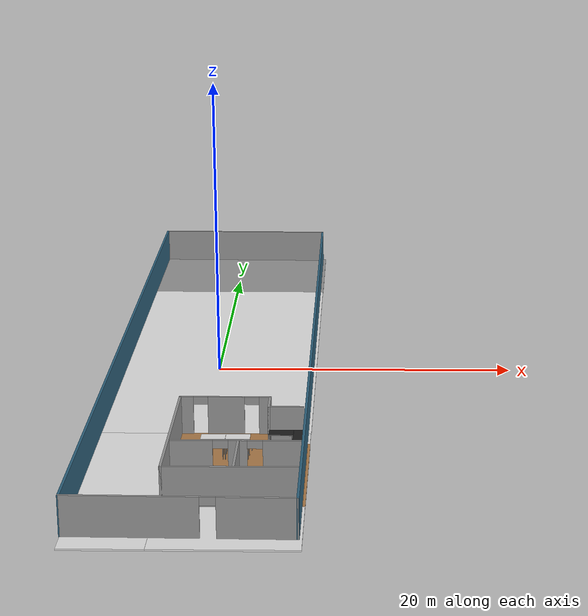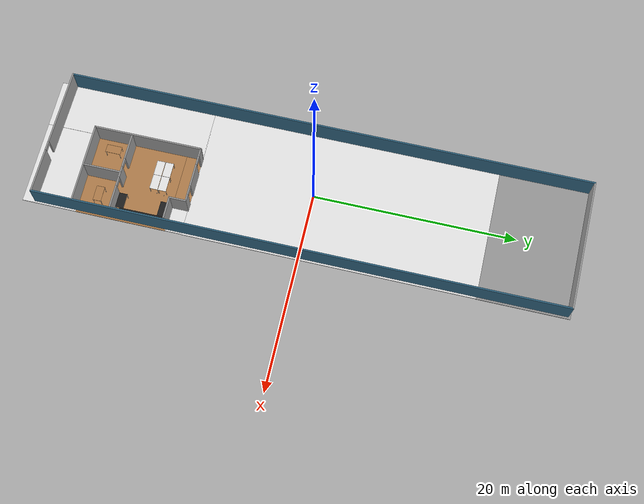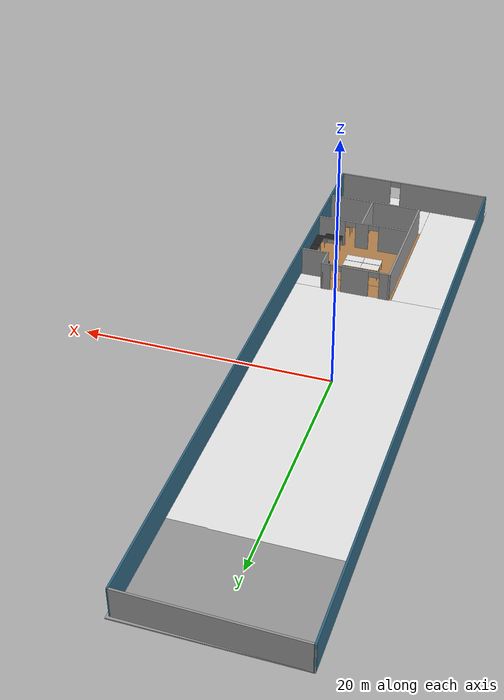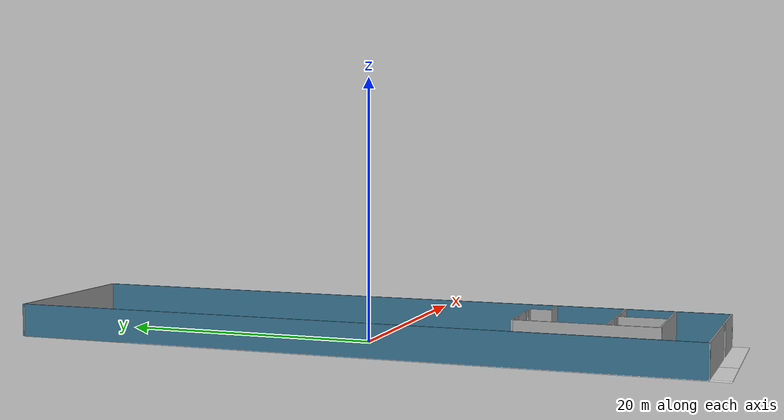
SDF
<?xml version='1.0'?>
<sdf version='1.7'>
  <model name='ageve'>
    <link name='Wall_0'>
      <pose>-0.012617 -26.05 0 0 0 -0.016364</pose>
      <self_collide>0</self_collide>
      <enable_wind>0</enable_wind>
      <kinematic>0</kinematic>
      <visual name='Wall_0_Visual_0'>
        <pose>-2.69028 0 1.25 0 -0 0</pose>
        <geometry>
          <box>
            <size>7.70052 0.15 2.5</size>
          </box>
        </geometry>
        <material>
          <script>
            <uri>file://media/materials/scripts/gazebo.material</uri>
            <name>Gazebo/Grey</name>
          </script>
          <ambient>1 1 1 1</ambient>
          <shader type='pixel'/>
        </material>
        <meta>
          <layer>0</layer>
        </meta>
        <transparency>0</transparency>
        <cast_shadows>1</cast_shadows>
      </visual>
      <visual name='Wall_0_Visual_1'>
        <pose>4.30026 0 1.25 0 -0 0</pose>
        <geometry>
          <box>
            <size>4.48056 0.15 2.5</size>
          </box>
        </geometry>
        <material>
          <script>
            <uri>file://media/materials/scripts/gazebo.material</uri>
            <name>Gazebo/Grey</name>
          </script>
          <ambient>1 1 1 1</ambient>
          <shader type='pixel'/>
        </material>
        <meta>
          <layer>0</layer>
        </meta>
        <transparency>0</transparency>
        <cast_shadows>1</cast_shadows>
      </visual>
      <visual name='Wall_0_Visual_2'>
        <pose>1.60998 0 2.25 0 -0 0</pose>
        <geometry>
          <box>
            <size>0.9 0.15 0.5</size>
          </box>
        </geometry>
        <material>
          <script>
            <uri>file://media/materials/scripts/gazebo.material</uri>
            <name>Gazebo/Grey</name>
          </script>
          <ambient>1 1 1 1</ambient>
          <shader type='pixel'/>
        </material>
        <meta>
          <layer>0</layer>
        </meta>
        <transparency>0</transparency>
        <cast_shadows>1</cast_shadows>
      </visual>
      <collision name='Wall_0_Collision_2'>
        <laser_retro>0</laser_retro>
        <max_contacts>10</max_contacts>
        <pose>1.60998 0 2.25 0 -0 0</pose>
        <geometry>
          <box>
            <size>0.9 0.15 0.5</size>
          </box>
        </geometry>
        <surface>
          <friction>
            <ode>
              <mu>1</mu>
              <mu2>1</mu2>
              <fdir1>0 0 0</fdir1>
              <slip1>0</slip1>
              <slip2>0</slip2>
            </ode>
            <torsional>
              <coefficient>1</coefficient>
              <patch_radius>0</patch_radius>
              <surface_radius>0</surface_radius>
              <use_patch_radius>1</use_patch_radius>
              <ode>
                <slip>0</slip>
              </ode>
            </torsional>
          </friction>
          <bounce>
            <restitution_coefficient>0</restitution_coefficient>
            <threshold>1e+06</threshold>
          </bounce>
          <contact>
            <collide_without_contact>0</collide_without_contact>
            <collide_without_contact_bitmask>1</collide_without_contact_bitmask>
            <collide_bitmask>1</collide_bitmask>
            <ode>
              <soft_cfm>0</soft_cfm>
              <soft_erp>0.2</soft_erp>
              <kp>1e+13</kp>
              <kd>1</kd>
              <max_vel>0.01</max_vel>
              <min_depth>0</min_depth>
            </ode>
            <bullet>
              <split_impulse>1</split_impulse>
              <split_impulse_penetration_threshold>-0.01</split_impulse_penetration_threshold>
              <soft_cfm>0</soft_cfm>
              <soft_erp>0.2</soft_erp>
              <kp>1e+13</kp>
              <kd>1</kd>
            </bullet>
          </contact>
        </surface>
      </collision>
      <collision name='Wall_0_Collision_0'>
        <laser_retro>0</laser_retro>
        <max_contacts>10</max_contacts>
        <pose>-2.69028 0 1.25 0 -0 0</pose>
        <geometry>
          <box>
            <size>7.70052 0.15 2.5</size>
          </box>
        </geometry>
        <surface>
          <friction>
            <ode>
              <mu>1</mu>
              <mu2>1</mu2>
              <fdir1>0 0 0</fdir1>
              <slip1>0</slip1>
              <slip2>0</slip2>
            </ode>
            <torsional>
              <coefficient>1</coefficient>
              <patch_radius>0</patch_radius>
              <surface_radius>0</surface_radius>
              <use_patch_radius>1</use_patch_radius>
              <ode>
                <slip>0</slip>
              </ode>
            </torsional>
          </friction>
          <bounce>
            <restitution_coefficient>0</restitution_coefficient>
            <threshold>1e+06</threshold>
          </bounce>
          <contact>
            <collide_without_contact>0</collide_without_contact>
            <collide_without_contact_bitmask>1</collide_without_contact_bitmask>
            <collide_bitmask>1</collide_bitmask>
            <ode>
              <soft_cfm>0</soft_cfm>
              <soft_erp>0.2</soft_erp>
              <kp>1e+13</kp>
              <kd>1</kd>
              <max_vel>0.01</max_vel>
              <min_depth>0</min_depth>
            </ode>
            <bullet>
              <split_impulse>1</split_impulse>
              <split_impulse_penetration_threshold>-0.01</split_impulse_penetration_threshold>
              <soft_cfm>0</soft_cfm>
              <soft_erp>0.2</soft_erp>
              <kp>1e+13</kp>
              <kd>1</kd>
            </bullet>
          </contact>
        </surface>
      </collision>
      <collision name='Wall_0_Collision_1'>
        <laser_retro>0</laser_retro>
        <max_contacts>10</max_contacts>
        <pose>4.30026 0 1.25 0 -0 0</pose>
        <geometry>
          <box>
            <size>4.48056 0.15 2.5</size>
          </box>
        </geometry>
        <surface>
          <friction>
            <ode>
              <mu>1</mu>
              <mu2>1</mu2>
              <fdir1>0 0 0</fdir1>
              <slip1>0</slip1>
              <slip2>0</slip2>
            </ode>
            <torsional>
              <coefficient>1</coefficient>
              <patch_radius>0</patch_radius>
              <surface_radius>0</surface_radius>
              <use_patch_radius>1</use_patch_radius>
              <ode>
                <slip>0</slip>
              </ode>
            </torsional>
          </friction>
          <bounce>
            <restitution_coefficient>0</restitution_coefficient>
            <threshold>1e+06</threshold>
          </bounce>
          <contact>
            <collide_without_contact>0</collide_without_contact>
            <collide_without_contact_bitmask>1</collide_without_contact_bitmask>
            <collide_bitmask>1</collide_bitmask>
            <ode>
              <soft_cfm>0</soft_cfm>
              <soft_erp>0.2</soft_erp>
              <kp>1e+13</kp>
              <kd>1</kd>
              <max_vel>0.01</max_vel>
              <min_depth>0</min_depth>
            </ode>
            <bullet>
              <split_impulse>1</split_impulse>
              <split_impulse_penetration_threshold>-0.01</split_impulse_penetration_threshold>
              <soft_cfm>0</soft_cfm>
              <soft_erp>0.2</soft_erp>
              <kp>1e+13</kp>
              <kd>1</kd>
            </bullet>
          </contact>
        </surface>
      </collision>
    </link>
    <link name='Wall_11'>
      <pose>2.68575 -20.1713 0 0 0 -1.5708</pose>
      <self_collide>0</self_collide>
      <enable_wind>0</enable_wind>
      <kinematic>0</kinematic>
      <visual name='Wall_11_Visual'>
        <pose>0 0 1.25 0 -0 0</pose>
        <geometry>
          <box>
            <size>3.75 0.15 2.5</size>
          </box>
        </geometry>
        <material>
          <script>
            <uri>file://media/materials/scripts/gazebo.material</uri>
            <name>Gazebo/Grey</name>
          </script>
          <ambient>1 1 1 1</ambient>
          <shader type='pixel'/>
        </material>
        <meta>
          <layer>0</layer>
        </meta>
        <transparency>0</transparency>
        <cast_shadows>1</cast_shadows>
      </visual>
      <collision name='Wall_11_Collision'>
        <laser_retro>0</laser_retro>
        <max_contacts>10</max_contacts>
        <pose>0 0 1.25 0 -0 0</pose>
        <geometry>
          <box>
            <size>3.75 0.15 2.5</size>
          </box>
        </geometry>
        <surface>
          <friction>
            <ode>
              <mu>1</mu>
              <mu2>1</mu2>
              <fdir1>0 0 0</fdir1>
              <slip1>0</slip1>
              <slip2>0</slip2>
            </ode>
            <torsional>
              <coefficient>1</coefficient>
              <patch_radius>0</patch_radius>
              <surface_radius>0</surface_radius>
              <use_patch_radius>1</use_patch_radius>
              <ode>
                <slip>0</slip>
              </ode>
            </torsional>
          </friction>
          <bounce>
            <restitution_coefficient>0</restitution_coefficient>
            <threshold>1e+06</threshold>
          </bounce>
          <contact>
            <collide_without_contact>0</collide_without_contact>
            <collide_without_contact_bitmask>1</collide_without_contact_bitmask>
            <collide_bitmask>1</collide_bitmask>
            <ode>
              <soft_cfm>0</soft_cfm>
              <soft_erp>0.2</soft_erp>
              <kp>1e+13</kp>
              <kd>1</kd>
              <max_vel>0.01</max_vel>
              <min_depth>0</min_depth>
            </ode>
            <bullet>
              <split_impulse>1</split_impulse>
              <split_impulse_penetration_threshold>-0.01</split_impulse_penetration_threshold>
              <soft_cfm>0</soft_cfm>
              <soft_erp>0.2</soft_erp>
              <kp>1e+13</kp>
              <kd>1</kd>
            </bullet>
          </contact>
        </surface>
      </collision>
    </link>
    <link name='Wall_13'>
      <pose>6.47851 -0.1058 0 0 -0 1.5708</pose>
      <self_collide>0</self_collide>
      <enable_wind>0</enable_wind>
      <kinematic>0</kinematic>
      <visual name='Wall_13_Visual'>
        <pose>0 0 1.25 0 -0 0</pose>
        <geometry>
          <box>
            <size>52.25 0.15 2.5</size>
          </box>
        </geometry>
        <material>
          <ambient>0.19 0.4 0.51 1</ambient>
          <diffuse>0.19 0.4 0.51 1</diffuse>
          <specular>0.19 0.4 0.51 1</specular>
          <emissive>0.19 0.4 0.51 1</emissive>
          <shader type='pixel'/>
          <script>
            <name>ModelPreview_1::Wall_9::Wall_9_Visual_MATERIAL_</name>
            <uri>__default__</uri>
          </script>
        </material>
        <meta>
          <layer>0</layer>
        </meta>
        <transparency>0</transparency>
        <cast_shadows>1</cast_shadows>
      </visual>
      <collision name='Wall_13_Collision'>
        <laser_retro>0</laser_retro>
        <max_contacts>10</max_contacts>
        <pose>0 0 1.25 0 -0 0</pose>
        <geometry>
          <box>
            <size>52.25 0.15 2.5</size>
          </box>
        </geometry>
        <surface>
          <friction>
            <ode>
              <mu>1</mu>
              <mu2>1</mu2>
              <fdir1>0 0 0</fdir1>
              <slip1>0</slip1>
              <slip2>0</slip2>
            </ode>
            <torsional>
              <coefficient>1</coefficient>
              <patch_radius>0</patch_radius>
              <surface_radius>0</surface_radius>
              <use_patch_radius>1</use_patch_radius>
              <ode>
                <slip>0</slip>
              </ode>
            </torsional>
          </friction>
          <bounce>
            <restitution_coefficient>0</restitution_coefficient>
            <threshold>1e+06</threshold>
          </bounce>
          <contact>
            <collide_without_contact>0</collide_without_contact>
            <collide_without_contact_bitmask>1</collide_without_contact_bitmask>
            <collide_bitmask>1</collide_bitmask>
            <ode>
              <soft_cfm>0</soft_cfm>
              <soft_erp>0.2</soft_erp>
              <kp>1e+13</kp>
              <kd>1</kd>
              <max_vel>0.01</max_vel>
              <min_depth>0</min_depth>
            </ode>
            <bullet>
              <split_impulse>1</split_impulse>
              <split_impulse_penetration_threshold>-0.01</split_impulse_penetration_threshold>
              <soft_cfm>0</soft_cfm>
              <soft_erp>0.2</soft_erp>
              <kp>1e+13</kp>
              <kd>1</kd>
            </bullet>
          </contact>
        </surface>
      </collision>
    </link>
    <link name='Wall_14'>
      <pose>-0.012617 26.05 0 0 -0 3.12523</pose>
      <self_collide>0</self_collide>
      <enable_wind>0</enable_wind>
      <kinematic>0</kinematic>
      <visual name='Wall_14_Visual'>
        <pose>0 0 1.25 0 -0 0</pose>
        <geometry>
          <box>
            <size>13.0811 0.15 2.5</size>
          </box>
        </geometry>
        <material>
          <script>
            <uri>file://media/materials/scripts/gazebo.material</uri>
            <name>Gazebo/Grey</name>
          </script>
          <ambient>1 1 1 1</ambient>
          <shader type='pixel'/>
        </material>
        <meta>
          <layer>0</layer>
        </meta>
        <transparency>0</transparency>
        <cast_shadows>1</cast_shadows>
      </visual>
      <collision name='Wall_14_Collision'>
        <laser_retro>0</laser_retro>
        <max_contacts>10</max_contacts>
        <pose>0 0 1.25 0 -0 0</pose>
        <geometry>
          <box>
            <size>13.0811 0.15 2.5</size>
          </box>
        </geometry>
        <surface>
          <friction>
            <ode>
              <mu>1</mu>
              <mu2>1</mu2>
              <fdir1>0 0 0</fdir1>
              <slip1>0</slip1>
              <slip2>0</slip2>
            </ode>
            <torsional>
              <coefficient>1</coefficient>
              <patch_radius>0</patch_radius>
              <surface_radius>0</surface_radius>
              <use_patch_radius>1</use_patch_radius>
              <ode>
                <slip>0</slip>
              </ode>
            </torsional>
          </friction>
          <bounce>
            <restitution_coefficient>0</restitution_coefficient>
            <threshold>1e+06</threshold>
          </bounce>
          <contact>
            <collide_without_contact>0</collide_without_contact>
            <collide_without_contact_bitmask>1</collide_without_contact_bitmask>
            <collide_bitmask>1</collide_bitmask>
            <ode>
              <soft_cfm>0</soft_cfm>
              <soft_erp>0.2</soft_erp>
              <kp>1e+13</kp>
              <kd>1</kd>
              <max_vel>0.01</max_vel>
              <min_depth>0</min_depth>
            </ode>
            <bullet>
              <split_impulse>1</split_impulse>
              <split_impulse_penetration_threshold>-0.01</split_impulse_penetration_threshold>
              <soft_cfm>0</soft_cfm>
              <soft_erp>0.2</soft_erp>
              <kp>1e+13</kp>
              <kd>1</kd>
            </bullet>
          </contact>
        </surface>
      </collision>
    </link>
    <link name='Wall_15'>
      <pose>-6.47729 0.1058 0 0 0 -1.5708</pose>
      <self_collide>0</self_collide>
      <enable_wind>0</enable_wind>
      <kinematic>0</kinematic>
      <visual name='Wall_15_Visual'>
        <pose>0 0 1.25 0 -0 0</pose>
        <geometry>
          <box>
            <size>52.25 0.15 2.5</size>
          </box>
        </geometry>
        <material>
          <ambient>0.19 0.4 0.51 1</ambient>
          <diffuse>0.19 0.4 0.51 1</diffuse>
          <specular>0.19 0.4 0.51 1</specular>
          <emissive>0.19 0.4 0.51 1</emissive>
          <shader type='pixel'/>
          <script>
            <name>ModelPreview_1::Wall_9::Wall_9_Visual_MATERIAL_</name>
            <uri>__default__</uri>
          </script>
        </material>
        <meta>
          <layer>0</layer>
        </meta>
        <transparency>0</transparency>
        <cast_shadows>1</cast_shadows>
      </visual>
      <collision name='Wall_15_Collision'>
        <laser_retro>0</laser_retro>
        <max_contacts>10</max_contacts>
        <pose>0 0 1.25 0 -0 0</pose>
        <geometry>
          <box>
            <size>52.25 0.15 2.5</size>
          </box>
        </geometry>
        <surface>
          <friction>
            <ode>
              <mu>1</mu>
              <mu2>1</mu2>
              <fdir1>0 0 0</fdir1>
              <slip1>0</slip1>
              <slip2>0</slip2>
            </ode>
            <torsional>
              <coefficient>1</coefficient>
              <patch_radius>0</patch_radius>
              <surface_radius>0</surface_radius>
              <use_patch_radius>1</use_patch_radius>
              <ode>
                <slip>0</slip>
              </ode>
            </torsional>
          </friction>
          <bounce>
            <restitution_coefficient>0</restitution_coefficient>
            <threshold>1e+06</threshold>
          </bounce>
          <contact>
            <collide_without_contact>0</collide_without_contact>
            <collide_without_contact_bitmask>1</collide_without_contact_bitmask>
            <collide_bitmask>1</collide_bitmask>
            <ode>
              <soft_cfm>0</soft_cfm>
              <soft_erp>0.2</soft_erp>
              <kp>1e+13</kp>
              <kd>1</kd>
              <max_vel>0.01</max_vel>
              <min_depth>0</min_depth>
            </ode>
            <bullet>
              <split_impulse>1</split_impulse>
              <split_impulse_penetration_threshold>-0.01</split_impulse_penetration_threshold>
              <soft_cfm>0</soft_cfm>
              <soft_erp>0.2</soft_erp>
              <kp>1e+13</kp>
              <kd>1</kd>
            </bullet>
          </contact>
        </surface>
      </collision>
    </link>
    <link name='Wall_2'>
      <pose>2.54723 -18.366 0 0 -0 0</pose>
      <self_collide>0</self_collide>
      <enable_wind>0</enable_wind>
      <kinematic>0</kinematic>
      <visual name='Wall_2_Visual_0'>
        <pose>-2.61461 0 1.25 0 -0 0</pose>
        <geometry>
          <box>
            <size>2.52079 0.15 2.5</size>
          </box>
        </geometry>
        <material>
          <script>
            <uri>file://media/materials/scripts/gazebo.material</uri>
            <name>Gazebo/Grey</name>
          </script>
          <ambient>1 1 1 1</ambient>
          <shader type='pixel'/>
        </material>
        <meta>
          <layer>0</layer>
        </meta>
        <transparency>0</transparency>
        <cast_shadows>1</cast_shadows>
      </visual>
      <visual name='Wall_2_Visual_1'>
        <pose>0.108959 0 1.25 0 -0 0</pose>
        <geometry>
          <box>
            <size>1.12634 0.15 2.5</size>
          </box>
        </geometry>
        <material>
          <script>
            <uri>file://media/materials/scripts/gazebo.material</uri>
            <name>Gazebo/Grey</name>
          </script>
          <ambient>1 1 1 1</ambient>
          <shader type='pixel'/>
        </material>
        <meta>
          <layer>0</layer>
        </meta>
        <transparency>0</transparency>
        <cast_shadows>1</cast_shadows>
      </visual>
      <visual name='Wall_2_Visual_3'>
        <pose>-0.904212 0 2.25 0 -0 0</pose>
        <geometry>
          <box>
            <size>0.9 0.15 0.5</size>
          </box>
        </geometry>
        <material>
          <script>
            <uri>file://media/materials/scripts/gazebo.material</uri>
            <name>Gazebo/Grey</name>
          </script>
          <ambient>1 1 1 1</ambient>
          <shader type='pixel'/>
        </material>
        <meta>
          <layer>0</layer>
        </meta>
        <transparency>0</transparency>
        <cast_shadows>1</cast_shadows>
      </visual>
      <visual name='Wall_2_Visual_2'>
        <pose>2.72357 0 1.25 0 -0 0</pose>
        <geometry>
          <box>
            <size>2.30287 0.15 2.5</size>
          </box>
        </geometry>
        <material>
          <script>
            <uri>file://media/materials/scripts/gazebo.material</uri>
            <name>Gazebo/Grey</name>
          </script>
          <ambient>1 1 1 1</ambient>
          <shader type='pixel'/>
        </material>
        <meta>
          <layer>0</layer>
        </meta>
        <transparency>0</transparency>
        <cast_shadows>1</cast_shadows>
      </visual>
      <visual name='Wall_2_Visual_4'>
        <pose>1.12213 0 2.25 0 -0 0</pose>
        <geometry>
          <box>
            <size>0.9 0.15 0.5</size>
          </box>
        </geometry>
        <material>
          <script>
            <uri>file://media/materials/scripts/gazebo.material</uri>
            <name>Gazebo/Grey</name>
          </script>
          <ambient>1 1 1 1</ambient>
          <shader type='pixel'/>
        </material>
        <meta>
          <layer>0</layer>
        </meta>
        <transparency>0</transparency>
        <cast_shadows>1</cast_shadows>
      </visual>
      <collision name='Wall_2_Collision_0'>
        <laser_retro>0</laser_retro>
        <max_contacts>10</max_contacts>
        <pose>-2.61461 0 1.25 0 -0 0</pose>
        <geometry>
          <box>
            <size>2.52079 0.15 2.5</size>
          </box>
        </geometry>
        <surface>
          <friction>
            <ode>
              <mu>1</mu>
              <mu2>1</mu2>
              <fdir1>0 0 0</fdir1>
              <slip1>0</slip1>
              <slip2>0</slip2>
            </ode>
            <torsional>
              <coefficient>1</coefficient>
              <patch_radius>0</patch_radius>
              <surface_radius>0</surface_radius>
              <use_patch_radius>1</use_patch_radius>
              <ode>
                <slip>0</slip>
              </ode>
            </torsional>
          </friction>
          <bounce>
            <restitution_coefficient>0</restitution_coefficient>
            <threshold>1e+06</threshold>
          </bounce>
          <contact>
            <collide_without_contact>0</collide_without_contact>
            <collide_without_contact_bitmask>1</collide_without_contact_bitmask>
            <collide_bitmask>1</collide_bitmask>
            <ode>
              <soft_cfm>0</soft_cfm>
              <soft_erp>0.2</soft_erp>
              <kp>1e+13</kp>
              <kd>1</kd>
              <max_vel>0.01</max_vel>
              <min_depth>0</min_depth>
            </ode>
            <bullet>
              <split_impulse>1</split_impulse>
              <split_impulse_penetration_threshold>-0.01</split_impulse_penetration_threshold>
              <soft_cfm>0</soft_cfm>
              <soft_erp>0.2</soft_erp>
              <kp>1e+13</kp>
              <kd>1</kd>
            </bullet>
          </contact>
        </surface>
      </collision>
      <collision name='Wall_2_Collision_3'>
        <laser_retro>0</laser_retro>
        <max_contacts>10</max_contacts>
        <pose>-0.904212 0 2.25 0 -0 0</pose>
        <geometry>
          <box>
            <size>0.9 0.15 0.5</size>
          </box>
        </geometry>
        <surface>
          <friction>
            <ode>
              <mu>1</mu>
              <mu2>1</mu2>
              <fdir1>0 0 0</fdir1>
              <slip1>0</slip1>
              <slip2>0</slip2>
            </ode>
            <torsional>
              <coefficient>1</coefficient>
              <patch_radius>0</patch_radius>
              <surface_radius>0</surface_radius>
              <use_patch_radius>1</use_patch_radius>
              <ode>
                <slip>0</slip>
              </ode>
            </torsional>
          </friction>
          <bounce>
            <restitution_coefficient>0</restitution_coefficient>
            <threshold>1e+06</threshold>
          </bounce>
          <contact>
            <collide_without_contact>0</collide_without_contact>
            <collide_without_contact_bitmask>1</collide_without_contact_bitmask>
            <collide_bitmask>1</collide_bitmask>
            <ode>
              <soft_cfm>0</soft_cfm>
              <soft_erp>0.2</soft_erp>
              <kp>1e+13</kp>
              <kd>1</kd>
              <max_vel>0.01</max_vel>
              <min_depth>0</min_depth>
            </ode>
            <bullet>
              <split_impulse>1</split_impulse>
              <split_impulse_penetration_threshold>-0.01</split_impulse_penetration_threshold>
              <soft_cfm>0</soft_cfm>
              <soft_erp>0.2</soft_erp>
              <kp>1e+13</kp>
              <kd>1</kd>
            </bullet>
          </contact>
        </surface>
      </collision>
      <collision name='Wall_2_Collision_1'>
        <laser_retro>0</laser_retro>
        <max_contacts>10</max_contacts>
        <pose>0.108959 0 1.25 0 -0 0</pose>
        <geometry>
          <box>
            <size>1.12634 0.15 2.5</size>
          </box>
        </geometry>
        <surface>
          <friction>
            <ode>
              <mu>1</mu>
              <mu2>1</mu2>
              <fdir1>0 0 0</fdir1>
              <slip1>0</slip1>
              <slip2>0</slip2>
            </ode>
            <torsional>
              <coefficient>1</coefficient>
              <patch_radius>0</patch_radius>
              <surface_radius>0</surface_radius>
              <use_patch_radius>1</use_patch_radius>
              <ode>
                <slip>0</slip>
              </ode>
            </torsional>
          </friction>
          <bounce>
            <restitution_coefficient>0</restitution_coefficient>
            <threshold>1e+06</threshold>
          </bounce>
          <contact>
            <collide_without_contact>0</collide_without_contact>
            <collide_without_contact_bitmask>1</collide_without_contact_bitmask>
            <collide_bitmask>1</collide_bitmask>
            <ode>
              <soft_cfm>0</soft_cfm>
              <soft_erp>0.2</soft_erp>
              <kp>1e+13</kp>
              <kd>1</kd>
              <max_vel>0.01</max_vel>
              <min_depth>0</min_depth>
            </ode>
            <bullet>
              <split_impulse>1</split_impulse>
              <split_impulse_penetration_threshold>-0.01</split_impulse_penetration_threshold>
              <soft_cfm>0</soft_cfm>
              <soft_erp>0.2</soft_erp>
              <kp>1e+13</kp>
              <kd>1</kd>
            </bullet>
          </contact>
        </surface>
      </collision>
      <collision name='Wall_2_Collision_2'>
        <laser_retro>0</laser_retro>
        <max_contacts>10</max_contacts>
        <pose>2.72357 0 1.25 0 -0 0</pose>
        <geometry>
          <box>
            <size>2.30287 0.15 2.5</size>
          </box>
        </geometry>
        <surface>
          <friction>
            <ode>
              <mu>1</mu>
              <mu2>1</mu2>
              <fdir1>0 0 0</fdir1>
              <slip1>0</slip1>
              <slip2>0</slip2>
            </ode>
            <torsional>
              <coefficient>1</coefficient>
              <patch_radius>0</patch_radius>
              <surface_radius>0</surface_radius>
              <use_patch_radius>1</use_patch_radius>
              <ode>
                <slip>0</slip>
              </ode>
            </torsional>
          </friction>
          <bounce>
            <restitution_coefficient>0</restitution_coefficient>
            <threshold>1e+06</threshold>
          </bounce>
          <contact>
            <collide_without_contact>0</collide_without_contact>
            <collide_without_contact_bitmask>1</collide_without_contact_bitmask>
            <collide_bitmask>1</collide_bitmask>
            <ode>
              <soft_cfm>0</soft_cfm>
              <soft_erp>0.2</soft_erp>
              <kp>1e+13</kp>
              <kd>1</kd>
              <max_vel>0.01</max_vel>
              <min_depth>0</min_depth>
            </ode>
            <bullet>
              <split_impulse>1</split_impulse>
              <split_impulse_penetration_threshold>-0.01</split_impulse_penetration_threshold>
              <soft_cfm>0</soft_cfm>
              <soft_erp>0.2</soft_erp>
              <kp>1e+13</kp>
              <kd>1</kd>
            </bullet>
          </contact>
        </surface>
      </collision>
      <collision name='Wall_2_Collision_4'>
        <laser_retro>0</laser_retro>
        <max_contacts>10</max_contacts>
        <pose>1.12213 0 2.25 0 -0 0</pose>
        <geometry>
          <box>
            <size>0.9 0.15 0.5</size>
          </box>
        </geometry>
        <surface>
          <friction>
            <ode>
              <mu>1</mu>
              <mu2>1</mu2>
              <fdir1>0 0 0</fdir1>
              <slip1>0</slip1>
              <slip2>0</slip2>
            </ode>
            <torsional>
              <coefficient>1</coefficient>
              <patch_radius>0</patch_radius>
              <surface_radius>0</surface_radius>
              <use_patch_radius>1</use_patch_radius>
              <ode>
                <slip>0</slip>
              </ode>
            </torsional>
          </friction>
          <bounce>
            <restitution_coefficient>0</restitution_coefficient>
            <threshold>1e+06</threshold>
          </bounce>
          <contact>
            <collide_without_contact>0</collide_without_contact>
            <collide_without_contact_bitmask>1</collide_without_contact_bitmask>
            <collide_bitmask>1</collide_bitmask>
            <ode>
              <soft_cfm>0</soft_cfm>
              <soft_erp>0.2</soft_erp>
              <kp>1e+13</kp>
              <kd>1</kd>
              <max_vel>0.01</max_vel>
              <min_depth>0</min_depth>
            </ode>
            <bullet>
              <split_impulse>1</split_impulse>
              <split_impulse_penetration_threshold>-0.01</split_impulse_penetration_threshold>
              <soft_cfm>0</soft_cfm>
              <soft_erp>0.2</soft_erp>
              <kp>1e+13</kp>
              <kd>1</kd>
            </bullet>
          </contact>
        </surface>
      </collision>
    </link>
    <link name='Wall_4'>
      <pose>1.37549 -11.4935 0 0 -0 0</pose>
      <self_collide>0</self_collide>
      <enable_wind>0</enable_wind>
      <kinematic>0</kinematic>
      <visual name='Wall_4_Visual_0'>
        <pose>-2.43007 0 1.25 0 -0 0</pose>
        <geometry>
          <box>
            <size>0.889859 0.15 2.5</size>
          </box>
        </geometry>
        <material>
          <script>
            <uri>file://media/materials/scripts/gazebo.material</uri>
            <name>Gazebo/Grey</name>
          </script>
          <ambient>1 1 1 1</ambient>
          <shader type='pixel'/>
        </material>
        <meta>
          <layer>0</layer>
        </meta>
        <transparency>0</transparency>
        <cast_shadows>1</cast_shadows>
      </visual>
      <visual name='Wall_4_Visual_1'>
        <pose>0.056164 0 1.25 0 -0 0</pose>
        <geometry>
          <box>
            <size>2.28261 0.15 2.5</size>
          </box>
        </geometry>
        <material>
          <script>
            <uri>file://media/materials/scripts/gazebo.material</uri>
            <name>Gazebo/Grey</name>
          </script>
          <ambient>1 1 1 1</ambient>
          <shader type='pixel'/>
        </material>
        <meta>
          <layer>0</layer>
        </meta>
        <transparency>0</transparency>
        <cast_shadows>1</cast_shadows>
      </visual>
      <visual name='Wall_4_Visual_2'>
        <pose>2.48623 0 1.25 0 -0 0</pose>
        <geometry>
          <box>
            <size>0.777532 0.15 2.5</size>
          </box>
        </geometry>
        <material>
          <script>
            <uri>file://media/materials/scripts/gazebo.material</uri>
            <name>Gazebo/Grey</name>
          </script>
          <ambient>1 1 1 1</ambient>
          <shader type='pixel'/>
        </material>
        <meta>
          <layer>0</layer>
        </meta>
        <transparency>0</transparency>
        <cast_shadows>1</cast_shadows>
      </visual>
      <visual name='Wall_4_Visual_3'>
        <pose>-1.53514 0 2.25 0 -0 0</pose>
        <geometry>
          <box>
            <size>0.9 0.15 0.5</size>
          </box>
        </geometry>
        <material>
          <script>
            <uri>file://media/materials/scripts/gazebo.material</uri>
            <name>Gazebo/Grey</name>
          </script>
          <ambient>1 1 1 1</ambient>
          <shader type='pixel'/>
        </material>
        <meta>
          <layer>0</layer>
        </meta>
        <transparency>0</transparency>
        <cast_shadows>1</cast_shadows>
      </visual>
      <visual name='Wall_4_Visual_4'>
        <pose>1.64747 0 2.25 0 -0 0</pose>
        <geometry>
          <box>
            <size>0.9 0.15 0.5</size>
          </box>
        </geometry>
        <material>
          <script>
            <uri>file://media/materials/scripts/gazebo.material</uri>
            <name>Gazebo/Grey</name>
          </script>
          <ambient>1 1 1 1</ambient>
          <shader type='pixel'/>
        </material>
        <meta>
          <layer>0</layer>
        </meta>
        <transparency>0</transparency>
        <cast_shadows>1</cast_shadows>
      </visual>
      <collision name='Wall_4_Collision_0'>
        <laser_retro>0</laser_retro>
        <max_contacts>10</max_contacts>
        <pose>-2.43007 0 1.25 0 -0 0</pose>
        <geometry>
          <box>
            <size>0.889859 0.15 2.5</size>
          </box>
        </geometry>
        <surface>
          <friction>
            <ode>
              <mu>1</mu>
              <mu2>1</mu2>
              <fdir1>0 0 0</fdir1>
              <slip1>0</slip1>
              <slip2>0</slip2>
            </ode>
            <torsional>
              <coefficient>1</coefficient>
              <patch_radius>0</patch_radius>
              <surface_radius>0</surface_radius>
              <use_patch_radius>1</use_patch_radius>
              <ode>
                <slip>0</slip>
              </ode>
            </torsional>
          </friction>
          <bounce>
            <restitution_coefficient>0</restitution_coefficient>
            <threshold>1e+06</threshold>
          </bounce>
          <contact>
            <collide_without_contact>0</collide_without_contact>
            <collide_without_contact_bitmask>1</collide_without_contact_bitmask>
            <collide_bitmask>1</collide_bitmask>
            <ode>
              <soft_cfm>0</soft_cfm>
              <soft_erp>0.2</soft_erp>
              <kp>1e+13</kp>
              <kd>1</kd>
              <max_vel>0.01</max_vel>
              <min_depth>0</min_depth>
            </ode>
            <bullet>
              <split_impulse>1</split_impulse>
              <split_impulse_penetration_threshold>-0.01</split_impulse_penetration_threshold>
              <soft_cfm>0</soft_cfm>
              <soft_erp>0.2</soft_erp>
              <kp>1e+13</kp>
              <kd>1</kd>
            </bullet>
          </contact>
        </surface>
      </collision>
      <collision name='Wall_4_Collision_1'>
        <laser_retro>0</laser_retro>
        <max_contacts>10</max_contacts>
        <pose>0.056164 0 1.25 0 -0 0</pose>
        <geometry>
          <box>
            <size>2.28261 0.15 2.5</size>
          </box>
        </geometry>
        <surface>
          <friction>
            <ode>
              <mu>1</mu>
              <mu2>1</mu2>
              <fdir1>0 0 0</fdir1>
              <slip1>0</slip1>
              <slip2>0</slip2>
            </ode>
            <torsional>
              <coefficient>1</coefficient>
              <patch_radius>0</patch_radius>
              <surface_radius>0</surface_radius>
              <use_patch_radius>1</use_patch_radius>
              <ode>
                <slip>0</slip>
              </ode>
            </torsional>
          </friction>
          <bounce>
            <restitution_coefficient>0</restitution_coefficient>
            <threshold>1e+06</threshold>
          </bounce>
          <contact>
            <collide_without_contact>0</collide_without_contact>
            <collide_without_contact_bitmask>1</collide_without_contact_bitmask>
            <collide_bitmask>1</collide_bitmask>
            <ode>
              <soft_cfm>0</soft_cfm>
              <soft_erp>0.2</soft_erp>
              <kp>1e+13</kp>
              <kd>1</kd>
              <max_vel>0.01</max_vel>
              <min_depth>0</min_depth>
            </ode>
            <bullet>
              <split_impulse>1</split_impulse>
              <split_impulse_penetration_threshold>-0.01</split_impulse_penetration_threshold>
              <soft_cfm>0</soft_cfm>
              <soft_erp>0.2</soft_erp>
              <kp>1e+13</kp>
              <kd>1</kd>
            </bullet>
          </contact>
        </surface>
      </collision>
      <collision name='Wall_4_Collision_4'>
        <laser_retro>0</laser_retro>
        <max_contacts>10</max_contacts>
        <pose>1.64747 0 2.25 0 -0 0</pose>
        <geometry>
          <box>
            <size>0.9 0.15 0.5</size>
          </box>
        </geometry>
        <surface>
          <friction>
            <ode>
              <mu>1</mu>
              <mu2>1</mu2>
              <fdir1>0 0 0</fdir1>
              <slip1>0</slip1>
              <slip2>0</slip2>
            </ode>
            <torsional>
              <coefficient>1</coefficient>
              <patch_radius>0</patch_radius>
              <surface_radius>0</surface_radius>
              <use_patch_radius>1</use_patch_radius>
              <ode>
                <slip>0</slip>
              </ode>
            </torsional>
          </friction>
          <bounce>
            <restitution_coefficient>0</restitution_coefficient>
            <threshold>1e+06</threshold>
          </bounce>
          <contact>
            <collide_without_contact>0</collide_without_contact>
            <collide_without_contact_bitmask>1</collide_without_contact_bitmask>
            <collide_bitmask>1</collide_bitmask>
            <ode>
              <soft_cfm>0</soft_cfm>
              <soft_erp>0.2</soft_erp>
              <kp>1e+13</kp>
              <kd>1</kd>
              <max_vel>0.01</max_vel>
              <min_depth>0</min_depth>
            </ode>
            <bullet>
              <split_impulse>1</split_impulse>
              <split_impulse_penetration_threshold>-0.01</split_impulse_penetration_threshold>
              <soft_cfm>0</soft_cfm>
              <soft_erp>0.2</soft_erp>
              <kp>1e+13</kp>
              <kd>1</kd>
            </bullet>
          </contact>
        </surface>
      </collision>
      <collision name='Wall_4_Collision_2'>
        <laser_retro>0</laser_retro>
        <max_contacts>10</max_contacts>
        <pose>2.48623 0 1.25 0 -0 0</pose>
        <geometry>
          <box>
            <size>0.777532 0.15 2.5</size>
          </box>
        </geometry>
        <surface>
          <friction>
            <ode>
              <mu>1</mu>
              <mu2>1</mu2>
              <fdir1>0 0 0</fdir1>
              <slip1>0</slip1>
              <slip2>0</slip2>
            </ode>
            <torsional>
              <coefficient>1</coefficient>
              <patch_radius>0</patch_radius>
              <surface_radius>0</surface_radius>
              <use_patch_radius>1</use_patch_radius>
              <ode>
                <slip>0</slip>
              </ode>
            </torsional>
          </friction>
          <bounce>
            <restitution_coefficient>0</restitution_coefficient>
            <threshold>1e+06</threshold>
          </bounce>
          <contact>
            <collide_without_contact>0</collide_without_contact>
            <collide_without_contact_bitmask>1</collide_without_contact_bitmask>
            <collide_bitmask>1</collide_bitmask>
            <ode>
              <soft_cfm>0</soft_cfm>
              <soft_erp>0.2</soft_erp>
              <kp>1e+13</kp>
              <kd>1</kd>
              <max_vel>0.01</max_vel>
              <min_depth>0</min_depth>
            </ode>
            <bullet>
              <split_impulse>1</split_impulse>
              <split_impulse_penetration_threshold>-0.01</split_impulse_penetration_threshold>
              <soft_cfm>0</soft_cfm>
              <soft_erp>0.2</soft_erp>
              <kp>1e+13</kp>
              <kd>1</kd>
            </bullet>
          </contact>
        </surface>
      </collision>
      <collision name='Wall_4_Collision_3'>
        <laser_retro>0</laser_retro>
        <max_contacts>10</max_contacts>
        <pose>-1.53514 0 2.25 0 -0 0</pose>
        <geometry>
          <box>
            <size>0.9 0.15 0.5</size>
          </box>
        </geometry>
        <surface>
          <friction>
            <ode>
              <mu>1</mu>
              <mu2>1</mu2>
              <fdir1>0 0 0</fdir1>
              <slip1>0</slip1>
              <slip2>0</slip2>
            </ode>
            <torsional>
              <coefficient>1</coefficient>
              <patch_radius>0</patch_radius>
              <surface_radius>0</surface_radius>
              <use_patch_radius>1</use_patch_radius>
              <ode>
                <slip>0</slip>
              </ode>
            </torsional>
          </friction>
          <bounce>
            <restitution_coefficient>0</restitution_coefficient>
            <threshold>1e+06</threshold>
          </bounce>
          <contact>
            <collide_without_contact>0</collide_without_contact>
            <collide_without_contact_bitmask>1</collide_without_contact_bitmask>
            <collide_bitmask>1</collide_bitmask>
            <ode>
              <soft_cfm>0</soft_cfm>
              <soft_erp>0.2</soft_erp>
              <kp>1e+13</kp>
              <kd>1</kd>
              <max_vel>0.01</max_vel>
              <min_depth>0</min_depth>
            </ode>
            <bullet>
              <split_impulse>1</split_impulse>
              <split_impulse_penetration_threshold>-0.01</split_impulse_penetration_threshold>
              <soft_cfm>0</soft_cfm>
              <soft_erp>0.2</soft_erp>
              <kp>1e+13</kp>
              <kd>1</kd>
            </bullet>
          </contact>
        </surface>
      </collision>
    </link>
    <link name='Wall_5'>
      <pose>4.17549 -12.2935 0 0 0 -1.5708</pose>
      <self_collide>0</self_collide>
      <enable_wind>0</enable_wind>
      <kinematic>0</kinematic>
      <visual name='Wall_5_Visual'>
        <pose>0 0 1.25 0 -0 0</pose>
        <geometry>
          <box>
            <size>1.75 0.15 2.5</size>
          </box>
        </geometry>
        <material>
          <script>
            <uri>file://media/materials/scripts/gazebo.material</uri>
            <name>Gazebo/Grey</name>
          </script>
          <ambient>1 1 1 1</ambient>
          <shader type='pixel'/>
        </material>
        <meta>
          <layer>0</layer>
        </meta>
        <transparency>0</transparency>
        <cast_shadows>1</cast_shadows>
      </visual>
      <collision name='Wall_5_Collision'>
        <laser_retro>0</laser_retro>
        <max_contacts>10</max_contacts>
        <pose>0 0 1.25 0 -0 0</pose>
        <geometry>
          <box>
            <size>1.75 0.15 2.5</size>
          </box>
        </geometry>
        <surface>
          <friction>
            <ode>
              <mu>1</mu>
              <mu2>1</mu2>
              <fdir1>0 0 0</fdir1>
              <slip1>0</slip1>
              <slip2>0</slip2>
            </ode>
            <torsional>
              <coefficient>1</coefficient>
              <patch_radius>0</patch_radius>
              <surface_radius>0</surface_radius>
              <use_patch_radius>1</use_patch_radius>
              <ode>
                <slip>0</slip>
              </ode>
            </torsional>
          </friction>
          <bounce>
            <restitution_coefficient>0</restitution_coefficient>
            <threshold>1e+06</threshold>
          </bounce>
          <contact>
            <collide_without_contact>0</collide_without_contact>
            <collide_without_contact_bitmask>1</collide_without_contact_bitmask>
            <collide_bitmask>1</collide_bitmask>
            <ode>
              <soft_cfm>0</soft_cfm>
              <soft_erp>0.2</soft_erp>
              <kp>1e+13</kp>
              <kd>1</kd>
              <max_vel>0.01</max_vel>
              <min_depth>0</min_depth>
            </ode>
            <bullet>
              <split_impulse>1</split_impulse>
              <split_impulse_penetration_threshold>-0.01</split_impulse_penetration_threshold>
              <soft_cfm>0</soft_cfm>
              <soft_erp>0.2</soft_erp>
              <kp>1e+13</kp>
              <kd>1</kd>
            </bullet>
          </contact>
        </surface>
      </collision>
    </link>
    <link name='Wall_6'>
      <pose>5.22549 -13.0935 0 0 -0 0</pose>
      <self_collide>0</self_collide>
      <enable_wind>0</enable_wind>
      <kinematic>0</kinematic>
      <visual name='Wall_6_Visual'>
        <pose>0 0 1.25 0 -0 0</pose>
        <geometry>
          <box>
            <size>2.25 0.15 2.5</size>
          </box>
        </geometry>
        <material>
          <script>
            <uri>file://media/materials/scripts/gazebo.material</uri>
            <name>Gazebo/Grey</name>
          </script>
          <ambient>1 1 1 1</ambient>
          <shader type='pixel'/>
        </material>
        <meta>
          <layer>0</layer>
        </meta>
        <transparency>0</transparency>
        <cast_shadows>1</cast_shadows>
      </visual>
      <collision name='Wall_6_Collision'>
        <laser_retro>0</laser_retro>
        <max_contacts>10</max_contacts>
        <pose>0 0 1.25 0 -0 0</pose>
        <geometry>
          <box>
            <size>2.25 0.15 2.5</size>
          </box>
        </geometry>
        <surface>
          <friction>
            <ode>
              <mu>1</mu>
              <mu2>1</mu2>
              <fdir1>0 0 0</fdir1>
              <slip1>0</slip1>
              <slip2>0</slip2>
            </ode>
            <torsional>
              <coefficient>1</coefficient>
              <patch_radius>0</patch_radius>
              <surface_radius>0</surface_radius>
              <use_patch_radius>1</use_patch_radius>
              <ode>
                <slip>0</slip>
              </ode>
            </torsional>
          </friction>
          <bounce>
            <restitution_coefficient>0</restitution_coefficient>
            <threshold>1e+06</threshold>
          </bounce>
          <contact>
            <collide_without_contact>0</collide_without_contact>
            <collide_without_contact_bitmask>1</collide_without_contact_bitmask>
            <collide_bitmask>1</collide_bitmask>
            <ode>
              <soft_cfm>0</soft_cfm>
              <soft_erp>0.2</soft_erp>
              <kp>1e+13</kp>
              <kd>1</kd>
              <max_vel>0.01</max_vel>
              <min_depth>0</min_depth>
            </ode>
            <bullet>
              <split_impulse>1</split_impulse>
              <split_impulse_penetration_threshold>-0.01</split_impulse_penetration_threshold>
              <soft_cfm>0</soft_cfm>
              <soft_erp>0.2</soft_erp>
              <kp>1e+13</kp>
              <kd>1</kd>
            </bullet>
          </contact>
        </surface>
      </collision>
    </link>
    <link name='Wall_8'>
      <pose>-1.42451 -16.7935 0 0 0 -1.5708</pose>
      <self_collide>0</self_collide>
      <enable_wind>0</enable_wind>
      <kinematic>0</kinematic>
      <visual name='Wall_8_Visual'>
        <pose>0 0 1.25 0 -0 0</pose>
        <geometry>
          <box>
            <size>10.75 0.15 2.5</size>
          </box>
        </geometry>
        <material>
          <script>
            <uri>file://media/materials/scripts/gazebo.material</uri>
            <name>Gazebo/Grey</name>
          </script>
          <ambient>1 1 1 1</ambient>
          <shader type='pixel'/>
        </material>
        <meta>
          <layer>0</layer>
        </meta>
        <transparency>0</transparency>
        <cast_shadows>1</cast_shadows>
      </visual>
      <collision name='Wall_8_Collision'>
        <laser_retro>0</laser_retro>
        <max_contacts>10</max_contacts>
        <pose>0 0 1.25 0 -0 0</pose>
        <geometry>
          <box>
            <size>10.75 0.15 2.5</size>
          </box>
        </geometry>
        <surface>
          <friction>
            <ode>
              <mu>1</mu>
              <mu2>1</mu2>
              <fdir1>0 0 0</fdir1>
              <slip1>0</slip1>
              <slip2>0</slip2>
            </ode>
            <torsional>
              <coefficient>1</coefficient>
              <patch_radius>0</patch_radius>
              <surface_radius>0</surface_radius>
              <use_patch_radius>1</use_patch_radius>
              <ode>
                <slip>0</slip>
              </ode>
            </torsional>
          </friction>
          <bounce>
            <restitution_coefficient>0</restitution_coefficient>
            <threshold>1e+06</threshold>
          </bounce>
          <contact>
            <collide_without_contact>0</collide_without_contact>
            <collide_without_contact_bitmask>1</collide_without_contact_bitmask>
            <collide_bitmask>1</collide_bitmask>
            <ode>
              <soft_cfm>0</soft_cfm>
              <soft_erp>0.2</soft_erp>
              <kp>1e+13</kp>
              <kd>1</kd>
              <max_vel>0.01</max_vel>
              <min_depth>0</min_depth>
            </ode>
            <bullet>
              <split_impulse>1</split_impulse>
              <split_impulse_penetration_threshold>-0.01</split_impulse_penetration_threshold>
              <soft_cfm>0</soft_cfm>
              <soft_erp>0.2</soft_erp>
              <kp>1e+13</kp>
              <kd>1</kd>
            </bullet>
          </contact>
        </surface>
      </collision>
    </link>
    <link name='Wall_9'>
      <pose>2.50049 -22.0935 0 0 -0 0</pose>
      <self_collide>0</self_collide>
      <enable_wind>0</enable_wind>
      <kinematic>0</kinematic>
      <visual name='Wall_9_Visual'>
        <pose>0 0 1.25 0 -0 0</pose>
        <geometry>
          <box>
            <size>8 0.15 2.5</size>
          </box>
        </geometry>
        <material>
          <script>
            <uri>file://media/materials/scripts/gazebo.material</uri>
            <name>Gazebo/Grey</name>
          </script>
          <ambient>1 1 1 1</ambient>
          <shader type='pixel'/>
        </material>
        <meta>
          <layer>0</layer>
        </meta>
        <transparency>0</transparency>
        <cast_shadows>1</cast_shadows>
      </visual>
      <collision name='Wall_9_Collision'>
        <laser_retro>0</laser_retro>
        <max_contacts>10</max_contacts>
        <pose>0 0 1.25 0 -0 0</pose>
        <geometry>
          <box>
            <size>8 0.15 2.5</size>
          </box>
        </geometry>
        <surface>
          <friction>
            <ode>
              <mu>1</mu>
              <mu2>1</mu2>
              <fdir1>0 0 0</fdir1>
              <slip1>0</slip1>
              <slip2>0</slip2>
            </ode>
            <torsional>
              <coefficient>1</coefficient>
              <patch_radius>0</patch_radius>
              <surface_radius>0</surface_radius>
              <use_patch_radius>1</use_patch_radius>
              <ode>
                <slip>0</slip>
              </ode>
            </torsional>
          </friction>
          <bounce>
            <restitution_coefficient>0</restitution_coefficient>
            <threshold>1e+06</threshold>
          </bounce>
          <contact>
            <collide_without_contact>0</collide_without_contact>
            <collide_without_contact_bitmask>1</collide_without_contact_bitmask>
            <collide_bitmask>1</collide_bitmask>
            <ode>
              <soft_cfm>0</soft_cfm>
              <soft_erp>0.2</soft_erp>
              <kp>1e+13</kp>
              <kd>1</kd>
              <max_vel>0.01</max_vel>
              <min_depth>0</min_depth>
            </ode>
            <bullet>
              <split_impulse>1</split_impulse>
              <split_impulse_penetration_threshold>-0.01</split_impulse_penetration_threshold>
              <soft_cfm>0</soft_cfm>
              <soft_erp>0.2</soft_erp>
              <kp>1e+13</kp>
              <kd>1</kd>
            </bullet>
          </contact>
        </surface>
      </collision>
    </link>
    <model name='ageve_floor'>
      <link name='link'>
        <self_collide>0</self_collide>
        <enable_wind>0</enable_wind>
        <kinematic>0</kinematic>
        <pose>-2.67 23 0 0 -0 0</pose>
        <gravity>1</gravity>
        <inertial>
          <mass>1</mass>
          <pose>0 0 0 0 -0 0</pose>
          <inertia>
            <ixx>1</ixx>
            <ixy>0</ixy>
            <ixz>0</ixz>
            <iyy>1</iyy>
            <iyz>0</iyz>
            <izz>1</izz>
          </inertia>
        </inertial>
        <visual name='visual'>
          <cast_shadows>0</cast_shadows>
          <geometry>
            <box>
              <size>13.2 9 0.1</size>
            </box>
          </geometry>
          <material>
            <shader type='pixel'>
              <normal_map>__default__</normal_map>
            </shader>
            <script>
              <name>Gazebo/Grey</name>
              <uri>__default__</uri>
            </script>
          </material>
          <pose>-0.08 0 0 0 -0 0</pose>
          <transparency>0</transparency>
        </visual>
        <collision name='collision'>
          <laser_retro>0</laser_retro>
          <max_contacts>10</max_contacts>
          <pose>-0.06 0 0 0 -0 0</pose>
          <geometry>
            <box>
              <size>13.2 9 0.1</size>
            </box>
          </geometry>
          <surface>
            <friction>
              <ode>
                <mu>1</mu>
                <mu2>1</mu2>
                <fdir1>0 0 0</fdir1>
                <slip1>0</slip1>
                <slip2>0</slip2>
              </ode>
              <torsional>
                <coefficient>1</coefficient>
                <patch_radius>0</patch_radius>
                <surface_radius>0</surface_radius>
                <use_patch_radius>1</use_patch_radius>
                <ode>
                  <slip>0</slip>
                </ode>
              </torsional>
            </friction>
            <bounce>
              <restitution_coefficient>0</restitution_coefficient>
              <threshold>1e+06</threshold>
            </bounce>
            <contact>
              <collide_without_contact>0</collide_without_contact>
              <collide_without_contact_bitmask>1</collide_without_contact_bitmask>
              <collide_bitmask>1</collide_bitmask>
              <ode>
                <soft_cfm>0</soft_cfm>
                <soft_erp>0.2</soft_erp>
                <kp>1e+13</kp>
                <kd>1</kd>
                <max_vel>0.01</max_vel>
                <min_depth>0</min_depth>
              </ode>
              <bullet>
                <split_impulse>1</split_impulse>
                <split_impulse_penetration_threshold>-0.01</split_impulse_penetration_threshold>
                <soft_cfm>0</soft_cfm>
                <soft_erp>0.2</soft_erp>
                <kp>1e+13</kp>
                <kd>1</kd>
              </bullet>
            </contact>
          </surface>
        </collision>
      </link>
      <link name='link_clone'>
        <self_collide>0</self_collide>
        <enable_wind>0</enable_wind>
        <kinematic>0</kinematic>
        <pose>-2.69731 4.16 0 0 -0 0</pose>
        <gravity>1</gravity>
        <inertial>
          <mass>1</mass>
          <pose>0 0 0 0 -0 0</pose>
          <inertia>
            <ixx>1</ixx>
            <ixy>0</ixy>
            <ixz>0</ixz>
            <iyy>1</iyy>
            <iyz>0</iyz>
            <izz>1</izz>
          </inertia>
        </inertial>
        <visual name='visual'>
          <cast_shadows>0</cast_shadows>
          <geometry>
            <box>
              <size>13.2 28.8 0.1</size>
            </box>
          </geometry>
          <material>
            <shader type='pixel'>
              <normal_map>__default__</normal_map>
            </shader>
            <script>
              <name>Gazebo/White</name>
              <uri>__default__</uri>
            </script>
          </material>
          <pose>-0.08 0 0 0 -0 0</pose>
          <transparency>0</transparency>
        </visual>
        <collision name='collision'>
          <laser_retro>0</laser_retro>
          <max_contacts>10</max_contacts>
          <pose>-0.06 0 0 0 -0 0</pose>
          <geometry>
            <box>
              <size>13.2 28.8 0.1</size>
            </box>
          </geometry>
          <surface>
            <friction>
              <ode>
                <mu>1</mu>
                <mu2>1</mu2>
                <fdir1>0 0 0</fdir1>
                <slip1>0</slip1>
                <slip2>0</slip2>
              </ode>
              <torsional>
                <coefficient>1</coefficient>
                <patch_radius>0</patch_radius>
                <surface_radius>0</surface_radius>
                <use_patch_radius>1</use_patch_radius>
                <ode>
                  <slip>0</slip>
                </ode>
              </torsional>
            </friction>
            <bounce>
              <restitution_coefficient>0</restitution_coefficient>
              <threshold>1e+06</threshold>
            </bounce>
            <contact>
              <collide_without_contact>0</collide_without_contact>
              <collide_without_contact_bitmask>1</collide_without_contact_bitmask>
              <collide_bitmask>1</collide_bitmask>
              <ode>
                <soft_cfm>0</soft_cfm>
                <soft_erp>0.2</soft_erp>
                <kp>1e+13</kp>
                <kd>1</kd>
                <max_vel>0.01</max_vel>
                <min_depth>0</min_depth>
              </ode>
              <bullet>
                <split_impulse>1</split_impulse>
                <split_impulse_penetration_threshold>-0.01</split_impulse_penetration_threshold>
                <soft_cfm>0</soft_cfm>
                <soft_erp>0.2</soft_erp>
                <kp>1e+13</kp>
                <kd>1</kd>
              </bullet>
            </contact>
          </surface>
        </collision>
      </link>
      <link name='link_clone_0'>
        <self_collide>0</self_collide>
        <enable_wind>0</enable_wind>
        <kinematic>0</kinematic>
        <pose>-0.3 -16.2948 0 0 -0 0</pose>
        <gravity>1</gravity>
        <inertial>
          <mass>1</mass>
          <pose>0 0 0 0 -0 0</pose>
          <inertia>
            <ixx>1</ixx>
            <ixy>0</ixy>
            <ixz>0</ixz>
            <iyy>1</iyy>
            <iyz>0</iyz>
            <izz>1</izz>
          </inertia>
        </inertial>
        <visual name='visual'>
          <cast_shadows>0</cast_shadows>
          <geometry>
            <box>
              <size>8.4 9 0.1</size>
            </box>
          </geometry>
          <material>
            <shader type='pixel'>
              <normal_map>__default__</normal_map>
            </shader>
            <script>
              <name>Gazebo/Wood</name>
              <uri>__default__</uri>
            </script>
          </material>
          <pose>-0.08 0 0 0 -0 0</pose>
          <transparency>0</transparency>
        </visual>
        <collision name='collision'>
          <laser_retro>0</laser_retro>
          <max_contacts>10</max_contacts>
          <pose>-0.06 0 0 0 -0 0</pose>
          <geometry>
            <box>
              <size>8.4 9 0.1</size>
            </box>
          </geometry>
          <surface>
            <friction>
              <ode>
                <mu>1</mu>
                <mu2>1</mu2>
                <fdir1>0 0 0</fdir1>
                <slip1>0</slip1>
                <slip2>0</slip2>
              </ode>
              <torsional>
                <coefficient>1</coefficient>
                <patch_radius>0</patch_radius>
                <surface_radius>0</surface_radius>
                <use_patch_radius>1</use_patch_radius>
                <ode>
                  <slip>0</slip>
                </ode>
              </torsional>
            </friction>
            <bounce>
              <restitution_coefficient>0</restitution_coefficient>
              <threshold>1e+06</threshold>
            </bounce>
            <contact>
              <collide_without_contact>0</collide_without_contact>
              <collide_without_contact_bitmask>1</collide_without_contact_bitmask>
              <collide_bitmask>1</collide_bitmask>
              <ode>
                <soft_cfm>0</soft_cfm>
                <soft_erp>0.2</soft_erp>
                <kp>1e+13</kp>
                <kd>1</kd>
                <max_vel>0.01</max_vel>
                <min_depth>0</min_depth>
              </ode>
              <bullet>
                <split_impulse>1</split_impulse>
                <split_impulse_penetration_threshold>-0.01</split_impulse_penetration_threshold>
                <soft_cfm>0</soft_cfm>
                <soft_erp>0.2</soft_erp>
                <kp>1e+13</kp>
                <kd>1</kd>
              </bullet>
            </contact>
          </surface>
        </collision>
      </link>
      <link name='link_clone_0_clone'>
        <self_collide>0</self_collide>
        <enable_wind>0</enable_wind>
        <kinematic>0</kinematic>
        <pose>-1.58 -11 0 0 -0 0</pose>
        <gravity>1</gravity>
        <inertial>
          <mass>1</mass>
          <pose>0 0 0 0 -0 0</pose>
          <inertia>
            <ixx>1</ixx>
            <ixy>0</ixy>
            <ixz>0</ixz>
            <iyy>1</iyy>
            <iyz>0</iyz>
            <izz>1</izz>
          </inertia>
        </inertial>
        <visual name='visual'>
          <cast_shadows>0</cast_shadows>
          <geometry>
            <box>
              <size>5.8 1.6 0.1</size>
            </box>
          </geometry>
          <material>
            <shader type='pixel'>
              <normal_map>__default__</normal_map>
            </shader>
            <script>
              <name>Gazebo/Wood</name>
              <uri>__default__</uri>
            </script>
          </material>
          <pose>-0.08 0 0 0 -0 0</pose>
          <transparency>0</transparency>
        </visual>
        <collision name='collision'>
          <laser_retro>0</laser_retro>
          <max_contacts>10</max_contacts>
          <pose>-0.06 0 0 0 -0 0</pose>
          <geometry>
            <box>
              <size>5.8 1.6 0.1</size>
            </box>
          </geometry>
          <surface>
            <friction>
              <ode>
                <mu>1</mu>
                <mu2>1</mu2>
                <fdir1>0 0 0</fdir1>
                <slip1>0</slip1>
                <slip2>0</slip2>
              </ode>
              <torsional>
                <coefficient>1</coefficient>
                <patch_radius>0</patch_radius>
                <surface_radius>0</surface_radius>
                <use_patch_radius>1</use_patch_radius>
                <ode>
                  <slip>0</slip>
                </ode>
              </torsional>
            </friction>
            <bounce>
              <restitution_coefficient>0</restitution_coefficient>
              <threshold>1e+06</threshold>
            </bounce>
            <contact>
              <collide_without_contact>0</collide_without_contact>
              <collide_without_contact_bitmask>1</collide_without_contact_bitmask>
              <collide_bitmask>1</collide_bitmask>
              <ode>
                <soft_cfm>0</soft_cfm>
                <soft_erp>0.2</soft_erp>
                <kp>1e+13</kp>
                <kd>1</kd>
                <max_vel>0.01</max_vel>
                <min_depth>0</min_depth>
              </ode>
              <bullet>
                <split_impulse>1</split_impulse>
                <split_impulse_penetration_threshold>-0.01</split_impulse_penetration_threshold>
                <soft_cfm>0</soft_cfm>
                <soft_erp>0.2</soft_erp>
                <kp>1e+13</kp>
                <kd>1</kd>
              </bullet>
            </contact>
          </surface>
        </collision>
      </link>
      <link name='link_clone_clone'>
        <self_collide>0</self_collide>
        <enable_wind>0</enable_wind>
        <kinematic>0</kinematic>
        <pose>-6.92 -18.18 0 0 -0 0</pose>
        <gravity>1</gravity>
        <inertial>
          <mass>1</mass>
          <pose>0 0 0 0 -0 0</pose>
          <inertia>
            <ixx>1</ixx>
            <ixy>0</ixy>
            <ixz>0</ixz>
            <iyy>1</iyy>
            <iyz>0</iyz>
            <izz>1</izz>
          </inertia>
        </inertial>
        <visual name='visual'>
          <cast_shadows>0</cast_shadows>
          <geometry>
            <box>
              <size>4.8 16 0.1</size>
            </box>
          </geometry>
          <material>
            <shader type='pixel'>
              <normal_map>__default__</normal_map>
            </shader>
            <script>
              <name>Gazebo/White</name>
              <uri>__default__</uri>
            </script>
          </material>
          <pose>-0.08 0 0 0 -0 0</pose>
          <transparency>0</transparency>
        </visual>
        <collision name='collision'>
          <laser_retro>0</laser_retro>
          <max_contacts>10</max_contacts>
          <pose>-0.06 0 0 0 -0 0</pose>
          <geometry>
            <box>
              <size>4.8 16 0.1</size>
            </box>
          </geometry>
          <surface>
            <friction>
              <ode>
                <mu>1</mu>
                <mu2>1</mu2>
                <fdir1>0 0 0</fdir1>
                <slip1>0</slip1>
                <slip2>0</slip2>
              </ode>
              <torsional>
                <coefficient>1</coefficient>
                <patch_radius>0</patch_radius>
                <surface_radius>0</surface_radius>
                <use_patch_radius>1</use_patch_radius>
                <ode>
                  <slip>0</slip>
                </ode>
              </torsional>
            </friction>
            <bounce>
              <restitution_coefficient>0</restitution_coefficient>
              <threshold>1e+06</threshold>
            </bounce>
            <contact>
              <collide_without_contact>0</collide_without_contact>
              <collide_without_contact_bitmask>1</collide_without_contact_bitmask>
              <collide_bitmask>1</collide_bitmask>
              <ode>
                <soft_cfm>0</soft_cfm>
                <soft_erp>0.2</soft_erp>
                <kp>1e+13</kp>
                <kd>1</kd>
                <max_vel>0.01</max_vel>
                <min_depth>0</min_depth>
              </ode>
              <bullet>
                <split_impulse>1</split_impulse>
                <split_impulse_penetration_threshold>-0.01</split_impulse_penetration_threshold>
                <soft_cfm>0</soft_cfm>
                <soft_erp>0.2</soft_erp>
                <kp>1e+13</kp>
                <kd>1</kd>
              </bullet>
            </contact>
          </surface>
        </collision>
      </link>
      <link name='link_clone_clone_clone'>
        <self_collide>0</self_collide>
        <enable_wind>0</enable_wind>
        <kinematic>0</kinematic>
        <pose>2.57811 -11.04 0 0 -0 0</pose>
        <gravity>1</gravity>
        <inertial>
          <mass>1</mass>
          <pose>0 0 0 0 -0 0</pose>
          <inertia>
            <ixx>1</ixx>
            <ixy>0</ixy>
            <ixz>0</ixz>
            <iyy>1</iyy>
            <iyz>0</iyz>
            <izz>1</izz>
          </inertia>
        </inertial>
        <visual name='visual'>
          <cast_shadows>0</cast_shadows>
          <geometry>
            <box>
              <size>2.6 1.6 0.1</size>
            </box>
          </geometry>
          <material>
            <shader type='pixel'>
              <normal_map>__default__</normal_map>
            </shader>
            <script>
              <name>Gazebo/White</name>
              <uri>__default__</uri>
            </script>
          </material>
          <pose>-0.08 0 0 0 -0 0</pose>
          <transparency>0</transparency>
        </visual>
        <collision name='collision'>
          <laser_retro>0</laser_retro>
          <max_contacts>10</max_contacts>
          <pose>-0.06 0 0 0 -0 0</pose>
          <geometry>
            <box>
              <size>2.6 1.6 0.1</size>
            </box>
          </geometry>
          <surface>
            <friction>
              <ode>
                <mu>1</mu>
                <mu2>1</mu2>
                <fdir1>0 0 0</fdir1>
                <slip1>0</slip1>
                <slip2>0</slip2>
              </ode>
              <torsional>
                <coefficient>1</coefficient>
                <patch_radius>0</patch_radius>
                <surface_radius>0</surface_radius>
                <use_patch_radius>1</use_patch_radius>
                <ode>
                  <slip>0</slip>
                </ode>
              </torsional>
            </friction>
            <bounce>
              <restitution_coefficient>0</restitution_coefficient>
              <threshold>1e+06</threshold>
            </bounce>
            <contact>
              <collide_without_contact>0</collide_without_contact>
              <collide_without_contact_bitmask>1</collide_without_contact_bitmask>
              <collide_bitmask>1</collide_bitmask>
              <ode>
                <soft_cfm>0</soft_cfm>
                <soft_erp>0.2</soft_erp>
                <kp>1e+13</kp>
                <kd>1</kd>
                <max_vel>0.01</max_vel>
                <min_depth>0</min_depth>
              </ode>
              <bullet>
                <split_impulse>1</split_impulse>
                <split_impulse_penetration_threshold>-0.01</split_impulse_penetration_threshold>
                <soft_cfm>0</soft_cfm>
                <soft_erp>0.2</soft_erp>
                <kp>1e+13</kp>
                <kd>1</kd>
              </bullet>
            </contact>
          </surface>
        </collision>
      </link>
      <link name='link_clone_clone_clone_0'>
        <self_collide>0</self_collide>
        <enable_wind>0</enable_wind>
        <kinematic>0</kinematic>
        <pose>-0.313896 -23.48 0 0 -0 0</pose>
        <gravity>1</gravity>
        <inertial>
          <mass>1</mass>
          <pose>0 0 0 0 -0 0</pose>
          <inertia>
            <ixx>1</ixx>
            <ixy>0</ixy>
            <ixz>0</ixz>
            <iyy>1</iyy>
            <iyz>0</iyz>
            <izz>1</izz>
          </inertia>
        </inertial>
        <visual name='visual'>
          <cast_shadows>0</cast_shadows>
          <geometry>
            <box>
              <size>8.4 5.4 0.1</size>
            </box>
          </geometry>
          <material>
            <shader type='pixel'>
              <normal_map>__default__</normal_map>
            </shader>
            <script>
              <name>Gazebo/White</name>
              <uri>__default__</uri>
            </script>
          </material>
          <pose>-0.08 0 0 0 -0 0</pose>
          <transparency>0</transparency>
        </visual>
        <collision name='collision'>
          <laser_retro>0</laser_retro>
          <max_contacts>10</max_contacts>
          <pose>-0.06 0 0 0 -0 0</pose>
          <geometry>
            <box>
              <size>8.4 5.4 0.1</size>
            </box>
          </geometry>
          <surface>
            <friction>
              <ode>
                <mu>1</mu>
                <mu2>1</mu2>
                <fdir1>0 0 0</fdir1>
                <slip1>0</slip1>
                <slip2>0</slip2>
              </ode>
              <torsional>
                <coefficient>1</coefficient>
                <patch_radius>0</patch_radius>
                <surface_radius>0</surface_radius>
                <use_patch_radius>1</use_patch_radius>
                <ode>
                  <slip>0</slip>
                </ode>
              </torsional>
            </friction>
            <bounce>
              <restitution_coefficient>0</restitution_coefficient>
              <threshold>1e+06</threshold>
            </bounce>
            <contact>
              <collide_without_contact>0</collide_without_contact>
              <collide_without_contact_bitmask>1</collide_without_contact_bitmask>
              <collide_bitmask>1</collide_bitmask>
              <ode>
                <soft_cfm>0</soft_cfm>
                <soft_erp>0.2</soft_erp>
                <kp>1e+13</kp>
                <kd>1</kd>
                <max_vel>0.01</max_vel>
                <min_depth>0</min_depth>
              </ode>
              <bullet>
                <split_impulse>1</split_impulse>
                <split_impulse_penetration_threshold>-0.01</split_impulse_penetration_threshold>
                <soft_cfm>0</soft_cfm>
                <soft_erp>0.2</soft_erp>
                <kp>1e+13</kp>
                <kd>1</kd>
              </bullet>
            </contact>
          </surface>
        </collision>
      </link>
      <static>1</static>
      <allow_auto_disable>1</allow_auto_disable>
      <pose>2.895 -1.27755 0 0 -0 0</pose>
    </model>
    <model name='coke_can'>
      <link name='link'>
        <inertial>
          <pose>0 0 0.06 0 -0 0</pose>
          <mass>0.39</mass>
          <inertia>
            <ixx>0.00055575</ixx>
            <ixy>0</ixy>
            <ixz>0</ixz>
            <iyy>0.00055575</iyy>
            <iyz>0</iyz>
            <izz>0.0001755</izz>
          </inertia>
        </inertial>
        <collision name='collision'>
          <pose>0.003937 0.004724 -0.18 0 -0 0</pose>
          <geometry>
            <mesh>
              <uri>model://coke_can/meshes/coke_can.dae</uri>
            </mesh>
          </geometry>
          <surface>
            <friction>
              <ode>
                <mu>1</mu>
                <mu2>1</mu2>
              </ode>
              <torsional>
                <ode/>
              </torsional>
            </friction>
            <contact>
              <ode>
                <kp>1e+07</kp>
                <kd>1</kd>
                <min_depth>0.001</min_depth>
                <max_vel>0.1</max_vel>
              </ode>
            </contact>
            <bounce/>
          </surface>
          <max_contacts>10</max_contacts>
        </collision>
        <visual name='visual'>
          <pose>0.003937 0.004724 -0.18 0 -0 0</pose>
          <geometry>
            <mesh>
              <uri>model://coke_can/meshes/coke_can.dae</uri>
            </mesh>
          </geometry>
        </visual>
        <self_collide>0</self_collide>
        <enable_wind>0</enable_wind>
        <kinematic>0</kinematic>
      </link>
      <pose>3.18141 -14.1839 0 0 -0 0</pose>
    </model>
    <model name='coke_can_0'>
      <link name='link'>
        <inertial>
          <pose>0 0 0.06 0 -0 0</pose>
          <mass>0.39</mass>
          <inertia>
            <ixx>0.00055575</ixx>
            <ixy>0</ixy>
            <ixz>0</ixz>
            <iyy>0.00055575</iyy>
            <iyz>0</iyz>
            <izz>0.0001755</izz>
          </inertia>
        </inertial>
        <collision name='collision'>
          <pose>0.003937 0.004724 -0.18 0 -0 0</pose>
          <geometry>
            <mesh>
              <uri>model://coke_can/meshes/coke_can.dae</uri>
            </mesh>
          </geometry>
          <surface>
            <friction>
              <ode>
                <mu>1</mu>
                <mu2>1</mu2>
              </ode>
              <torsional>
                <ode/>
              </torsional>
            </friction>
            <contact>
              <ode>
                <kp>1e+07</kp>
                <kd>1</kd>
                <min_depth>0.001</min_depth>
                <max_vel>0.1</max_vel>
              </ode>
            </contact>
            <bounce/>
          </surface>
          <max_contacts>10</max_contacts>
        </collision>
        <visual name='visual'>
          <pose>0.003937 0.004724 -0.18 0 -0 0</pose>
          <geometry>
            <mesh>
              <uri>model://coke_can/meshes/coke_can.dae</uri>
            </mesh>
          </geometry>
        </visual>
        <self_collide>0</self_collide>
        <enable_wind>0</enable_wind>
        <kinematic>0</kinematic>
      </link>
      <pose>1.65987 -14.3374 0 0 -0 0</pose>
    </model>
    <model name='coke_can_1'>
      <link name='link'>
        <inertial>
          <pose>0 0 0.06 0 -0 0</pose>
          <mass>0.39</mass>
          <inertia>
            <ixx>0.00055575</ixx>
            <ixy>0</ixy>
            <ixz>0</ixz>
            <iyy>0.00055575</iyy>
            <iyz>0</iyz>
            <izz>0.0001755</izz>
          </inertia>
        </inertial>
        <collision name='collision'>
          <pose>0.003937 0.004724 -0.18 0 -0 0</pose>
          <geometry>
            <mesh>
              <uri>model://coke_can/meshes/coke_can.dae</uri>
            </mesh>
          </geometry>
          <surface>
            <friction>
              <ode>
                <mu>1</mu>
                <mu2>1</mu2>
              </ode>
              <torsional>
                <ode/>
              </torsional>
            </friction>
            <contact>
              <ode>
                <kp>1e+07</kp>
                <kd>1</kd>
                <min_depth>0.001</min_depth>
                <max_vel>0.1</max_vel>
              </ode>
            </contact>
            <bounce/>
          </surface>
          <max_contacts>10</max_contacts>
        </collision>
        <visual name='visual'>
          <pose>0.003937 0.004724 -0.18 0 -0 0</pose>
          <geometry>
            <mesh>
              <uri>model://coke_can/meshes/coke_can.dae</uri>
            </mesh>
          </geometry>
        </visual>
        <self_collide>0</self_collide>
        <enable_wind>0</enable_wind>
        <kinematic>0</kinematic>
      </link>
      <pose>3.07219 -14.9108 0 0 -0 0</pose>
    </model>
    <model name='coke_can_2'>
      <link name='link'>
        <inertial>
          <pose>0 0 0.06 0 -0 0</pose>
          <mass>0.39</mass>
          <inertia>
            <ixx>0.00055575</ixx>
            <ixy>0</ixy>
            <ixz>0</ixz>
            <iyy>0.00055575</iyy>
            <iyz>0</iyz>
            <izz>0.0001755</izz>
          </inertia>
        </inertial>
        <collision name='collision'>
          <pose>0.003937 0.004724 -0.18 0 -0 0</pose>
          <geometry>
            <mesh>
              <uri>model://coke_can/meshes/coke_can.dae</uri>
            </mesh>
          </geometry>
          <surface>
            <friction>
              <ode>
                <mu>1</mu>
                <mu2>1</mu2>
              </ode>
              <torsional>
                <ode/>
              </torsional>
            </friction>
            <contact>
              <ode>
                <kp>1e+07</kp>
                <kd>1</kd>
                <min_depth>0.001</min_depth>
                <max_vel>0.1</max_vel>
              </ode>
            </contact>
            <bounce/>
          </surface>
          <max_contacts>10</max_contacts>
        </collision>
        <visual name='visual'>
          <pose>0.003937 0.004724 -0.18 0 -0 0</pose>
          <geometry>
            <mesh>
              <uri>model://coke_can/meshes/coke_can.dae</uri>
            </mesh>
          </geometry>
        </visual>
        <self_collide>0</self_collide>
        <enable_wind>0</enable_wind>
        <kinematic>0</kinematic>
      </link>
      <pose>2.22945 -14.9439 0 0 -0 0</pose>
    </model>
    <model name='coke_can_3'>
      <link name='link'>
        <inertial>
          <pose>0 0 0.06 0 -0 0</pose>
          <mass>0.39</mass>
          <inertia>
            <ixx>0.00055575</ixx>
            <ixy>0</ixy>
            <ixz>0</ixz>
            <iyy>0.00055575</iyy>
            <iyz>0</iyz>
            <izz>0.0001755</izz>
          </inertia>
        </inertial>
        <collision name='collision'>
          <pose>0.003937 0.004724 -0.18 0 -0 0</pose>
          <geometry>
            <mesh>
              <uri>model://coke_can/meshes/coke_can.dae</uri>
            </mesh>
          </geometry>
          <surface>
            <friction>
              <ode>
                <mu>1</mu>
                <mu2>1</mu2>
              </ode>
              <torsional>
                <ode/>
              </torsional>
            </friction>
            <contact>
              <ode>
                <kp>1e+07</kp>
                <kd>1</kd>
                <min_depth>0.001</min_depth>
                <max_vel>0.1</max_vel>
              </ode>
            </contact>
            <bounce/>
          </surface>
          <max_contacts>10</max_contacts>
        </collision>
        <visual name='visual'>
          <pose>0.003937 0.004724 -0.18 0 -0 0</pose>
          <geometry>
            <mesh>
              <uri>model://coke_can/meshes/coke_can.dae</uri>
            </mesh>
          </geometry>
        </visual>
        <self_collide>0</self_collide>
        <enable_wind>0</enable_wind>
        <kinematic>0</kinematic>
      </link>
      <pose>0.713309 -15.2153 0 0 -0 0</pose>
    </model>
    <model name='table'>
      <static>1</static>
      <link name='link'>
        <collision name='surface'>
          <pose>0 0 1 0 -0 0</pose>
          <geometry>
            <box>
              <size>1.5 0.8 0.03</size>
            </box>
          </geometry>
          <surface>
            <friction>
              <ode>
                <mu>0.6</mu>
                <mu2>0.6</mu2>
              </ode>
              <torsional>
                <ode/>
              </torsional>
            </friction>
            <contact>
              <ode/>
            </contact>
            <bounce/>
          </surface>
          <max_contacts>10</max_contacts>
        </collision>
        <visual name='visual1'>
          <pose>0 0 1 0 -0 0</pose>
          <geometry>
            <box>
              <size>1.5 0.8 0.03</size>
            </box>
          </geometry>
          <material>
            <script>
              <uri>file://media/materials/scripts/gazebo.material</uri>
              <name>Gazebo/FlatBlack</name>
            </script>
          </material>
        </visual>
        <collision name='front_left_leg'>
          <pose>0.68 0.38 0.5 0 -0 0</pose>
          <geometry>
            <cylinder>
              <radius>0.02</radius>
              <length>1</length>
            </cylinder>
          </geometry>
          <max_contacts>10</max_contacts>
          <surface>
            <contact>
              <ode/>
            </contact>
            <bounce/>
            <friction>
              <torsional>
                <ode/>
              </torsional>
              <ode/>
            </friction>
          </surface>
        </collision>
        <visual name='front_left_leg'>
          <pose>0.68 0.38 0.5 0 -0 0</pose>
          <geometry>
            <cylinder>
              <radius>0.02</radius>
              <length>1</length>
            </cylinder>
          </geometry>
          <material>
            <script>
              <uri>file://media/materials/scripts/gazebo.material</uri>
              <name>Gazebo/FlatBlack</name>
            </script>
          </material>
        </visual>
        <collision name='front_right_leg'>
          <pose>0.68 -0.38 0.5 0 -0 0</pose>
          <geometry>
            <cylinder>
              <radius>0.02</radius>
              <length>1</length>
            </cylinder>
          </geometry>
          <max_contacts>10</max_contacts>
          <surface>
            <contact>
              <ode/>
            </contact>
            <bounce/>
            <friction>
              <torsional>
                <ode/>
              </torsional>
              <ode/>
            </friction>
          </surface>
        </collision>
        <visual name='front_right_leg'>
          <pose>0.68 -0.38 0.5 0 -0 0</pose>
          <geometry>
            <cylinder>
              <radius>0.02</radius>
              <length>1</length>
            </cylinder>
          </geometry>
          <material>
            <script>
              <uri>file://media/materials/scripts/gazebo.material</uri>
              <name>Gazebo/Grey</name>
            </script>
          </material>
        </visual>
        <collision name='back_right_leg'>
          <pose>-0.68 -0.38 0.5 0 -0 0</pose>
          <geometry>
            <cylinder>
              <radius>0.02</radius>
              <length>1</length>
            </cylinder>
          </geometry>
          <max_contacts>10</max_contacts>
          <surface>
            <contact>
              <ode/>
            </contact>
            <bounce/>
            <friction>
              <torsional>
                <ode/>
              </torsional>
              <ode/>
            </friction>
          </surface>
        </collision>
        <visual name='back_right_leg'>
          <pose>-0.68 -0.38 0.5 0 -0 0</pose>
          <geometry>
            <cylinder>
              <radius>0.02</radius>
              <length>1</length>
            </cylinder>
          </geometry>
          <material>
            <script>
              <uri>file://media/materials/scripts/gazebo.material</uri>
              <name>Gazebo/Grey</name>
            </script>
          </material>
        </visual>
        <collision name='back_left_leg'>
          <pose>-0.68 0.38 0.5 0 -0 0</pose>
          <geometry>
            <cylinder>
              <radius>0.02</radius>
              <length>1</length>
            </cylinder>
          </geometry>
          <max_contacts>10</max_contacts>
          <surface>
            <contact>
              <ode/>
            </contact>
            <bounce/>
            <friction>
              <torsional>
                <ode/>
              </torsional>
              <ode/>
            </friction>
          </surface>
        </collision>
        <visual name='back_left_leg'>
          <pose>-0.68 0.38 0.5 0 -0 0</pose>
          <geometry>
            <cylinder>
              <radius>0.02</radius>
              <length>1</length>
            </cylinder>
          </geometry>
          <material>
            <script>
              <uri>file://media/materials/scripts/gazebo.material</uri>
              <name>Gazebo/Grey</name>
            </script>
          </material>
        </visual>
        <self_collide>0</self_collide>
        <enable_wind>0</enable_wind>
        <kinematic>0</kinematic>
      </link>
      <pose>4.95824 -13.673 0 0 -0 0</pose>
    </model>
    <model name='table_0'>
      <static>1</static>
      <link name='link'>
        <collision name='surface'>
          <pose>0 0 1 0 -0 0</pose>
          <geometry>
            <box>
              <size>1.5 0.8 0.03</size>
            </box>
          </geometry>
          <surface>
            <friction>
              <ode>
                <mu>0.6</mu>
                <mu2>0.6</mu2>
              </ode>
              <torsional>
                <ode/>
              </torsional>
            </friction>
            <contact>
              <ode/>
            </contact>
            <bounce/>
          </surface>
          <max_contacts>10</max_contacts>
        </collision>
        <visual name='visual1'>
          <pose>0 0 1 0 -0 0</pose>
          <geometry>
            <box>
              <size>1.5 0.8 0.03</size>
            </box>
          </geometry>
          <material>
            <script>
              <uri>file://media/materials/scripts/gazebo.material</uri>
              <name>Gazebo/White</name>
            </script>
          </material>
        </visual>
        <collision name='front_left_leg'>
          <pose>0.68 0.38 0.5 0 -0 0</pose>
          <geometry>
            <cylinder>
              <radius>0.02</radius>
              <length>1</length>
            </cylinder>
          </geometry>
          <max_contacts>10</max_contacts>
          <surface>
            <contact>
              <ode/>
            </contact>
            <bounce/>
            <friction>
              <torsional>
                <ode/>
              </torsional>
              <ode/>
            </friction>
          </surface>
        </collision>
        <visual name='front_left_leg'>
          <pose>0.68 0.38 0.5 0 -0 0</pose>
          <geometry>
            <cylinder>
              <radius>0.02</radius>
              <length>1</length>
            </cylinder>
          </geometry>
          <material>
            <script>
              <uri>file://media/materials/scripts/gazebo.material</uri>
              <name>Gazebo/Grey</name>
            </script>
          </material>
        </visual>
        <collision name='front_right_leg'>
          <pose>0.68 -0.38 0.5 0 -0 0</pose>
          <geometry>
            <cylinder>
              <radius>0.02</radius>
              <length>1</length>
            </cylinder>
          </geometry>
          <max_contacts>10</max_contacts>
          <surface>
            <contact>
              <ode/>
            </contact>
            <bounce/>
            <friction>
              <torsional>
                <ode/>
              </torsional>
              <ode/>
            </friction>
          </surface>
        </collision>
        <visual name='front_right_leg'>
          <pose>0.68 -0.38 0.5 0 -0 0</pose>
          <geometry>
            <cylinder>
              <radius>0.02</radius>
              <length>1</length>
            </cylinder>
          </geometry>
          <material>
            <script>
              <uri>file://media/materials/scripts/gazebo.material</uri>
              <name>Gazebo/Grey</name>
            </script>
          </material>
        </visual>
        <collision name='back_right_leg'>
          <pose>-0.68 -0.38 0.5 0 -0 0</pose>
          <geometry>
            <cylinder>
              <radius>0.02</radius>
              <length>1</length>
            </cylinder>
          </geometry>
          <max_contacts>10</max_contacts>
          <surface>
            <contact>
              <ode/>
            </contact>
            <bounce/>
            <friction>
              <torsional>
                <ode/>
              </torsional>
              <ode/>
            </friction>
          </surface>
        </collision>
        <visual name='back_right_leg'>
          <pose>-0.68 -0.38 0.5 0 -0 0</pose>
          <geometry>
            <cylinder>
              <radius>0.02</radius>
              <length>1</length>
            </cylinder>
          </geometry>
          <material>
            <script>
              <uri>file://media/materials/scripts/gazebo.material</uri>
              <name>Gazebo/Grey</name>
            </script>
          </material>
        </visual>
        <collision name='back_left_leg'>
          <pose>-0.68 0.38 0.5 0 -0 0</pose>
          <geometry>
            <cylinder>
              <radius>0.02</radius>
              <length>1</length>
            </cylinder>
          </geometry>
          <max_contacts>10</max_contacts>
          <surface>
            <contact>
              <ode/>
            </contact>
            <bounce/>
            <friction>
              <torsional>
                <ode/>
              </torsional>
              <ode/>
            </friction>
          </surface>
        </collision>
        <visual name='back_left_leg'>
          <pose>-0.68 0.38 0.5 0 -0 0</pose>
          <geometry>
            <cylinder>
              <radius>0.02</radius>
              <length>1</length>
            </cylinder>
          </geometry>
          <material>
            <script>
              <uri>file://media/materials/scripts/gazebo.material</uri>
              <name>Gazebo/Grey</name>
            </script>
          </material>
        </visual>
        <self_collide>0</self_collide>
        <enable_wind>0</enable_wind>
        <kinematic>0</kinematic>
      </link>
      <pose>2.35731 -14.3119 0 0 -0 0</pose>
    </model>
    <model name='table_1'>
      <static>1</static>
      <link name='link'>
        <collision name='surface'>
          <pose>0 0 1 0 -0 0</pose>
          <geometry>
            <box>
              <size>1.5 0.8 0.03</size>
            </box>
          </geometry>
          <surface>
            <friction>
              <ode>
                <mu>0.6</mu>
                <mu2>0.6</mu2>
              </ode>
              <torsional>
                <ode/>
              </torsional>
            </friction>
            <contact>
              <ode/>
            </contact>
            <bounce/>
          </surface>
          <max_contacts>10</max_contacts>
        </collision>
        <visual name='visual1'>
          <pose>0 0 1 0 -0 0</pose>
          <geometry>
            <box>
              <size>1.5 0.8 0.03</size>
            </box>
          </geometry>
          <material>
            <script>
              <uri>file://media/materials/scripts/gazebo.material</uri>
              <name>Gazebo/White</name>
            </script>
          </material>
        </visual>
        <collision name='front_left_leg'>
          <pose>0.68 0.38 0.5 0 -0 0</pose>
          <geometry>
            <cylinder>
              <radius>0.02</radius>
              <length>1</length>
            </cylinder>
          </geometry>
          <max_contacts>10</max_contacts>
          <surface>
            <contact>
              <ode/>
            </contact>
            <bounce/>
            <friction>
              <torsional>
                <ode/>
              </torsional>
              <ode/>
            </friction>
          </surface>
        </collision>
        <visual name='front_left_leg'>
          <pose>0.68 0.38 0.5 0 -0 0</pose>
          <geometry>
            <cylinder>
              <radius>0.02</radius>
              <length>1</length>
            </cylinder>
          </geometry>
          <material>
            <script>
              <uri>file://media/materials/scripts/gazebo.material</uri>
              <name>Gazebo/Grey</name>
            </script>
          </material>
        </visual>
        <collision name='front_right_leg'>
          <pose>0.68 -0.38 0.5 0 -0 0</pose>
          <geometry>
            <cylinder>
              <radius>0.02</radius>
              <length>1</length>
            </cylinder>
          </geometry>
          <max_contacts>10</max_contacts>
          <surface>
            <contact>
              <ode/>
            </contact>
            <bounce/>
            <friction>
              <torsional>
                <ode/>
              </torsional>
              <ode/>
            </friction>
          </surface>
        </collision>
        <visual name='front_right_leg'>
          <pose>0.68 -0.38 0.5 0 -0 0</pose>
          <geometry>
            <cylinder>
              <radius>0.02</radius>
              <length>1</length>
            </cylinder>
          </geometry>
          <material>
            <script>
              <uri>file://media/materials/scripts/gazebo.material</uri>
              <name>Gazebo/Grey</name>
            </script>
          </material>
        </visual>
        <collision name='back_right_leg'>
          <pose>-0.68 -0.38 0.5 0 -0 0</pose>
          <geometry>
            <cylinder>
              <radius>0.02</radius>
              <length>1</length>
            </cylinder>
          </geometry>
          <max_contacts>10</max_contacts>
          <surface>
            <contact>
              <ode/>
            </contact>
            <bounce/>
            <friction>
              <torsional>
                <ode/>
              </torsional>
              <ode/>
            </friction>
          </surface>
        </collision>
        <visual name='back_right_leg'>
          <pose>-0.68 -0.38 0.5 0 -0 0</pose>
          <geometry>
            <cylinder>
              <radius>0.02</radius>
              <length>1</length>
            </cylinder>
          </geometry>
          <material>
            <script>
              <uri>file://media/materials/scripts/gazebo.material</uri>
              <name>Gazebo/Grey</name>
            </script>
          </material>
        </visual>
        <collision name='back_left_leg'>
          <pose>-0.68 0.38 0.5 0 -0 0</pose>
          <geometry>
            <cylinder>
              <radius>0.02</radius>
              <length>1</length>
            </cylinder>
          </geometry>
          <max_contacts>10</max_contacts>
          <surface>
            <contact>
              <ode/>
            </contact>
            <bounce/>
            <friction>
              <torsional>
                <ode/>
              </torsional>
              <ode/>
            </friction>
          </surface>
        </collision>
        <visual name='back_left_leg'>
          <pose>-0.68 0.38 0.5 0 -0 0</pose>
          <geometry>
            <cylinder>
              <radius>0.02</radius>
              <length>1</length>
            </cylinder>
          </geometry>
          <material>
            <script>
              <uri>file://media/materials/scripts/gazebo.material</uri>
              <name>Gazebo/Grey</name>
            </script>
          </material>
        </visual>
        <self_collide>0</self_collide>
        <enable_wind>0</enable_wind>
        <kinematic>0</kinematic>
      </link>
      <pose>0.844088 -14.3134 0 0 -0 0</pose>
    </model>
    <model name='table_2'>
      <static>1</static>
      <link name='link'>
        <collision name='surface'>
          <pose>0 0 1 0 -0 0</pose>
          <geometry>
            <box>
              <size>1.5 0.8 0.03</size>
            </box>
          </geometry>
          <surface>
            <friction>
              <ode>
                <mu>0.6</mu>
                <mu2>0.6</mu2>
              </ode>
              <torsional>
                <ode/>
              </torsional>
            </friction>
            <contact>
              <ode/>
            </contact>
            <bounce/>
          </surface>
          <max_contacts>10</max_contacts>
        </collision>
        <visual name='visual1'>
          <pose>0 0 1 0 -0 0</pose>
          <geometry>
            <box>
              <size>1.5 0.8 0.03</size>
            </box>
          </geometry>
          <material>
            <script>
              <uri>file://media/materials/scripts/gazebo.material</uri>
              <name>Gazebo/White</name>
            </script>
          </material>
        </visual>
        <collision name='front_left_leg'>
          <pose>0.68 0.38 0.5 0 -0 0</pose>
          <geometry>
            <cylinder>
              <radius>0.02</radius>
              <length>1</length>
            </cylinder>
          </geometry>
          <max_contacts>10</max_contacts>
          <surface>
            <contact>
              <ode/>
            </contact>
            <bounce/>
            <friction>
              <torsional>
                <ode/>
              </torsional>
              <ode/>
            </friction>
          </surface>
        </collision>
        <visual name='front_left_leg'>
          <pose>0.68 0.38 0.5 0 -0 0</pose>
          <geometry>
            <cylinder>
              <radius>0.02</radius>
              <length>1</length>
            </cylinder>
          </geometry>
          <material>
            <script>
              <uri>file://media/materials/scripts/gazebo.material</uri>
              <name>Gazebo/Grey</name>
            </script>
          </material>
        </visual>
        <collision name='front_right_leg'>
          <pose>0.68 -0.38 0.5 0 -0 0</pose>
          <geometry>
            <cylinder>
              <radius>0.02</radius>
              <length>1</length>
            </cylinder>
          </geometry>
          <max_contacts>10</max_contacts>
          <surface>
            <contact>
              <ode/>
            </contact>
            <bounce/>
            <friction>
              <torsional>
                <ode/>
              </torsional>
              <ode/>
            </friction>
          </surface>
        </collision>
        <visual name='front_right_leg'>
          <pose>0.68 -0.38 0.5 0 -0 0</pose>
          <geometry>
            <cylinder>
              <radius>0.02</radius>
              <length>1</length>
            </cylinder>
          </geometry>
          <material>
            <script>
              <uri>file://media/materials/scripts/gazebo.material</uri>
              <name>Gazebo/Grey</name>
            </script>
          </material>
        </visual>
        <collision name='back_right_leg'>
          <pose>-0.68 -0.38 0.5 0 -0 0</pose>
          <geometry>
            <cylinder>
              <radius>0.02</radius>
              <length>1</length>
            </cylinder>
          </geometry>
          <max_contacts>10</max_contacts>
          <surface>
            <contact>
              <ode/>
            </contact>
            <bounce/>
            <friction>
              <torsional>
                <ode/>
              </torsional>
              <ode/>
            </friction>
          </surface>
        </collision>
        <visual name='back_right_leg'>
          <pose>-0.68 -0.38 0.5 0 -0 0</pose>
          <geometry>
            <cylinder>
              <radius>0.02</radius>
              <length>1</length>
            </cylinder>
          </geometry>
          <material>
            <script>
              <uri>file://media/materials/scripts/gazebo.material</uri>
              <name>Gazebo/Grey</name>
            </script>
          </material>
        </visual>
        <collision name='back_left_leg'>
          <pose>-0.68 0.38 0.5 0 -0 0</pose>
          <geometry>
            <cylinder>
              <radius>0.02</radius>
              <length>1</length>
            </cylinder>
          </geometry>
          <max_contacts>10</max_contacts>
          <surface>
            <contact>
              <ode/>
            </contact>
            <bounce/>
            <friction>
              <torsional>
                <ode/>
              </torsional>
              <ode/>
            </friction>
          </surface>
        </collision>
        <visual name='back_left_leg'>
          <pose>-0.68 0.38 0.5 0 -0 0</pose>
          <geometry>
            <cylinder>
              <radius>0.02</radius>
              <length>1</length>
            </cylinder>
          </geometry>
          <material>
            <script>
              <uri>file://media/materials/scripts/gazebo.material</uri>
              <name>Gazebo/Grey</name>
            </script>
          </material>
        </visual>
        <self_collide>0</self_collide>
        <enable_wind>0</enable_wind>
        <kinematic>0</kinematic>
      </link>
      <pose>2.35589 -15.1519 0 0 -0 0</pose>
    </model>
    <model name='table_3'>
      <static>1</static>
      <link name='link'>
        <collision name='surface'>
          <pose>0 0 1 0 -0 0</pose>
          <geometry>
            <box>
              <size>1.5 0.8 0.03</size>
            </box>
          </geometry>
          <surface>
            <friction>
              <ode>
                <mu>0.6</mu>
                <mu2>0.6</mu2>
              </ode>
              <torsional>
                <ode/>
              </torsional>
            </friction>
            <contact>
              <ode/>
            </contact>
            <bounce/>
          </surface>
          <max_contacts>10</max_contacts>
        </collision>
        <visual name='visual1'>
          <pose>0 0 1 0 -0 0</pose>
          <geometry>
            <box>
              <size>1.5 0.8 0.03</size>
            </box>
          </geometry>
          <material>
            <script>
              <uri>file://media/materials/scripts/gazebo.material</uri>
              <name>Gazebo/White</name>
            </script>
          </material>
        </visual>
        <collision name='front_left_leg'>
          <pose>0.68 0.38 0.5 0 -0 0</pose>
          <geometry>
            <cylinder>
              <radius>0.02</radius>
              <length>1</length>
            </cylinder>
          </geometry>
          <max_contacts>10</max_contacts>
          <surface>
            <contact>
              <ode/>
            </contact>
            <bounce/>
            <friction>
              <torsional>
                <ode/>
              </torsional>
              <ode/>
            </friction>
          </surface>
        </collision>
        <visual name='front_left_leg'>
          <pose>0.68 0.38 0.5 0 -0 0</pose>
          <geometry>
            <cylinder>
              <radius>0.02</radius>
              <length>1</length>
            </cylinder>
          </geometry>
          <material>
            <script>
              <uri>file://media/materials/scripts/gazebo.material</uri>
              <name>Gazebo/Grey</name>
            </script>
          </material>
        </visual>
        <collision name='front_right_leg'>
          <pose>0.68 -0.38 0.5 0 -0 0</pose>
          <geometry>
            <cylinder>
              <radius>0.02</radius>
              <length>1</length>
            </cylinder>
          </geometry>
          <max_contacts>10</max_contacts>
          <surface>
            <contact>
              <ode/>
            </contact>
            <bounce/>
            <friction>
              <torsional>
                <ode/>
              </torsional>
              <ode/>
            </friction>
          </surface>
        </collision>
        <visual name='front_right_leg'>
          <pose>0.68 -0.38 0.5 0 -0 0</pose>
          <geometry>
            <cylinder>
              <radius>0.02</radius>
              <length>1</length>
            </cylinder>
          </geometry>
          <material>
            <script>
              <uri>file://media/materials/scripts/gazebo.material</uri>
              <name>Gazebo/Grey</name>
            </script>
          </material>
        </visual>
        <collision name='back_right_leg'>
          <pose>-0.68 -0.38 0.5 0 -0 0</pose>
          <geometry>
            <cylinder>
              <radius>0.02</radius>
              <length>1</length>
            </cylinder>
          </geometry>
          <max_contacts>10</max_contacts>
          <surface>
            <contact>
              <ode/>
            </contact>
            <bounce/>
            <friction>
              <torsional>
                <ode/>
              </torsional>
              <ode/>
            </friction>
          </surface>
        </collision>
        <visual name='back_right_leg'>
          <pose>-0.68 -0.38 0.5 0 -0 0</pose>
          <geometry>
            <cylinder>
              <radius>0.02</radius>
              <length>1</length>
            </cylinder>
          </geometry>
          <material>
            <script>
              <uri>file://media/materials/scripts/gazebo.material</uri>
              <name>Gazebo/Grey</name>
            </script>
          </material>
        </visual>
        <collision name='back_left_leg'>
          <pose>-0.68 0.38 0.5 0 -0 0</pose>
          <geometry>
            <cylinder>
              <radius>0.02</radius>
              <length>1</length>
            </cylinder>
          </geometry>
          <max_contacts>10</max_contacts>
          <surface>
            <contact>
              <ode/>
            </contact>
            <bounce/>
            <friction>
              <torsional>
                <ode/>
              </torsional>
              <ode/>
            </friction>
          </surface>
        </collision>
        <visual name='back_left_leg'>
          <pose>-0.68 0.38 0.5 0 -0 0</pose>
          <geometry>
            <cylinder>
              <radius>0.02</radius>
              <length>1</length>
            </cylinder>
          </geometry>
          <material>
            <script>
              <uri>file://media/materials/scripts/gazebo.material</uri>
              <name>Gazebo/Grey</name>
            </script>
          </material>
        </visual>
        <self_collide>0</self_collide>
        <enable_wind>0</enable_wind>
        <kinematic>0</kinematic>
      </link>
      <pose>0.849179 -15.1597 0 0 -0 0</pose>
    </model>
    <model name='table_4'>
      <static>1</static>
      <link name='link'>
        <collision name='surface'>
          <pose>0 0 1 0 -0 0</pose>
          <geometry>
            <box>
              <size>1.5 0.8 0.03</size>
            </box>
          </geometry>
          <surface>
            <friction>
              <ode>
                <mu>0.6</mu>
                <mu2>0.6</mu2>
              </ode>
              <torsional>
                <ode/>
              </torsional>
            </friction>
            <contact>
              <ode/>
            </contact>
            <bounce/>
          </surface>
          <max_contacts>10</max_contacts>
        </collision>
        <visual name='visual1'>
          <pose>0 0 1 0 -0 0</pose>
          <geometry>
            <box>
              <size>1.5 0.8 0.03</size>
            </box>
          </geometry>
          <material>
            <script>
              <uri>file://media/materials/scripts/gazebo.material</uri>
              <name>Gazebo/Wood</name>
            </script>
          </material>
        </visual>
        <collision name='front_left_leg'>
          <pose>0.68 0.38 0.5 0 -0 0</pose>
          <geometry>
            <cylinder>
              <radius>0.02</radius>
              <length>1</length>
            </cylinder>
          </geometry>
          <max_contacts>10</max_contacts>
          <surface>
            <contact>
              <ode/>
            </contact>
            <bounce/>
            <friction>
              <torsional>
                <ode/>
              </torsional>
              <ode/>
            </friction>
          </surface>
        </collision>
        <visual name='front_left_leg'>
          <pose>0.68 0.38 0.5 0 -0 0</pose>
          <geometry>
            <cylinder>
              <radius>0.02</radius>
              <length>1</length>
            </cylinder>
          </geometry>
          <material>
            <script>
              <uri>file://media/materials/scripts/gazebo.material</uri>
              <name>Gazebo/Grey</name>
            </script>
          </material>
        </visual>
        <collision name='front_right_leg'>
          <pose>0.68 -0.38 0.5 0 -0 0</pose>
          <geometry>
            <cylinder>
              <radius>0.02</radius>
              <length>1</length>
            </cylinder>
          </geometry>
          <max_contacts>10</max_contacts>
          <surface>
            <contact>
              <ode/>
            </contact>
            <bounce/>
            <friction>
              <torsional>
                <ode/>
              </torsional>
              <ode/>
            </friction>
          </surface>
        </collision>
        <visual name='front_right_leg'>
          <pose>0.68 -0.38 0.5 0 -0 0</pose>
          <geometry>
            <cylinder>
              <radius>0.02</radius>
              <length>1</length>
            </cylinder>
          </geometry>
          <material>
            <script>
              <uri>file://media/materials/scripts/gazebo.material</uri>
              <name>Gazebo/Grey</name>
            </script>
          </material>
        </visual>
        <collision name='back_right_leg'>
          <pose>-0.68 -0.38 0.5 0 -0 0</pose>
          <geometry>
            <cylinder>
              <radius>0.02</radius>
              <length>1</length>
            </cylinder>
          </geometry>
          <max_contacts>10</max_contacts>
          <surface>
            <contact>
              <ode/>
            </contact>
            <bounce/>
            <friction>
              <torsional>
                <ode/>
              </torsional>
              <ode/>
            </friction>
          </surface>
        </collision>
        <visual name='back_right_leg'>
          <pose>-0.68 -0.38 0.5 0 -0 0</pose>
          <geometry>
            <cylinder>
              <radius>0.02</radius>
              <length>1</length>
            </cylinder>
          </geometry>
          <material>
            <script>
              <uri>file://media/materials/scripts/gazebo.material</uri>
              <name>Gazebo/Grey</name>
            </script>
          </material>
        </visual>
        <collision name='back_left_leg'>
          <pose>-0.68 0.38 0.5 0 -0 0</pose>
          <geometry>
            <cylinder>
              <radius>0.02</radius>
              <length>1</length>
            </cylinder>
          </geometry>
          <max_contacts>10</max_contacts>
          <surface>
            <contact>
              <ode/>
            </contact>
            <bounce/>
            <friction>
              <torsional>
                <ode/>
              </torsional>
              <ode/>
            </friction>
          </surface>
        </collision>
        <visual name='back_left_leg'>
          <pose>-0.68 0.38 0.5 0 -0 0</pose>
          <geometry>
            <cylinder>
              <radius>0.02</radius>
              <length>1</length>
            </cylinder>
          </geometry>
          <material>
            <script>
              <uri>file://media/materials/scripts/gazebo.material</uri>
              <name>Gazebo/Grey</name>
            </script>
          </material>
        </visual>
        <self_collide>0</self_collide>
        <enable_wind>0</enable_wind>
        <kinematic>0</kinematic>
      </link>
      <pose>4.74405 -20.153 0 0 -0 0</pose>
    </model>
    <model name='table_5'>
      <static>1</static>
      <link name='link'>
        <collision name='surface'>
          <pose>0 0 1 0 -0 0</pose>
          <geometry>
            <box>
              <size>1.5 0.8 0.03</size>
            </box>
          </geometry>
          <surface>
            <friction>
              <ode>
                <mu>0.6</mu>
                <mu2>0.6</mu2>
              </ode>
              <torsional>
                <ode/>
              </torsional>
            </friction>
            <contact>
              <ode/>
            </contact>
            <bounce/>
          </surface>
          <max_contacts>10</max_contacts>
        </collision>
        <visual name='visual1'>
          <pose>0 0 1 0 -0 0</pose>
          <geometry>
            <box>
              <size>1.5 0.8 0.03</size>
            </box>
          </geometry>
          <material>
            <script>
              <uri>file://media/materials/scripts/gazebo.material</uri>
              <name>Gazebo/Wood</name>
            </script>
          </material>
        </visual>
        <collision name='front_left_leg'>
          <pose>0.68 0.38 0.5 0 -0 0</pose>
          <geometry>
            <cylinder>
              <radius>0.02</radius>
              <length>1</length>
            </cylinder>
          </geometry>
          <max_contacts>10</max_contacts>
          <surface>
            <contact>
              <ode/>
            </contact>
            <bounce/>
            <friction>
              <torsional>
                <ode/>
              </torsional>
              <ode/>
            </friction>
          </surface>
        </collision>
        <visual name='front_left_leg'>
          <pose>0.68 0.38 0.5 0 -0 0</pose>
          <geometry>
            <cylinder>
              <radius>0.02</radius>
              <length>1</length>
            </cylinder>
          </geometry>
          <material>
            <script>
              <uri>file://media/materials/scripts/gazebo.material</uri>
              <name>Gazebo/Grey</name>
            </script>
          </material>
        </visual>
        <collision name='front_right_leg'>
          <pose>0.68 -0.38 0.5 0 -0 0</pose>
          <geometry>
            <cylinder>
              <radius>0.02</radius>
              <length>1</length>
            </cylinder>
          </geometry>
          <max_contacts>10</max_contacts>
          <surface>
            <contact>
              <ode/>
            </contact>
            <bounce/>
            <friction>
              <torsional>
                <ode/>
              </torsional>
              <ode/>
            </friction>
          </surface>
        </collision>
        <visual name='front_right_leg'>
          <pose>0.68 -0.38 0.5 0 -0 0</pose>
          <geometry>
            <cylinder>
              <radius>0.02</radius>
              <length>1</length>
            </cylinder>
          </geometry>
          <material>
            <script>
              <uri>file://media/materials/scripts/gazebo.material</uri>
              <name>Gazebo/Grey</name>
            </script>
          </material>
        </visual>
        <collision name='back_right_leg'>
          <pose>-0.68 -0.38 0.5 0 -0 0</pose>
          <geometry>
            <cylinder>
              <radius>0.02</radius>
              <length>1</length>
            </cylinder>
          </geometry>
          <max_contacts>10</max_contacts>
          <surface>
            <contact>
              <ode/>
            </contact>
            <bounce/>
            <friction>
              <torsional>
                <ode/>
              </torsional>
              <ode/>
            </friction>
          </surface>
        </collision>
        <visual name='back_right_leg'>
          <pose>-0.68 -0.38 0.5 0 -0 0</pose>
          <geometry>
            <cylinder>
              <radius>0.02</radius>
              <length>1</length>
            </cylinder>
          </geometry>
          <material>
            <script>
              <uri>file://media/materials/scripts/gazebo.material</uri>
              <name>Gazebo/Grey</name>
            </script>
          </material>
        </visual>
        <collision name='back_left_leg'>
          <pose>-0.68 0.38 0.5 0 -0 0</pose>
          <geometry>
            <cylinder>
              <radius>0.02</radius>
              <length>1</length>
            </cylinder>
          </geometry>
          <max_contacts>10</max_contacts>
          <surface>
            <contact>
              <ode/>
            </contact>
            <bounce/>
            <friction>
              <torsional>
                <ode/>
              </torsional>
              <ode/>
            </friction>
          </surface>
        </collision>
        <visual name='back_left_leg'>
          <pose>-0.68 0.38 0.5 0 -0 0</pose>
          <geometry>
            <cylinder>
              <radius>0.02</radius>
              <length>1</length>
            </cylinder>
          </geometry>
          <material>
            <script>
              <uri>file://media/materials/scripts/gazebo.material</uri>
              <name>Gazebo/Grey</name>
            </script>
          </material>
        </visual>
        <self_collide>0</self_collide>
        <enable_wind>0</enable_wind>
        <kinematic>0</kinematic>
      </link>
      <pose>-0.08807 -20.0746 0 0 -0 1.57079</pose>
    </model>
    <model name='table_5_clone'>
      <static>1</static>
      <link name='link'>
        <collision name='surface'>
          <pose>0 0 1 0 -0 0</pose>
          <geometry>
            <box>
              <size>1.5 0.8 0.03</size>
            </box>
          </geometry>
          <surface>
            <friction>
              <ode>
                <mu>0.6</mu>
                <mu2>0.6</mu2>
              </ode>
              <torsional>
                <ode/>
              </torsional>
            </friction>
            <contact>
              <ode/>
            </contact>
            <bounce/>
          </surface>
          <max_contacts>10</max_contacts>
        </collision>
        <visual name='visual1'>
          <pose>0 0 1 0 -0 0</pose>
          <geometry>
            <box>
              <size>1.5 0.8 0.03</size>
            </box>
          </geometry>
          <material>
            <script>
              <uri>file://media/materials/scripts/gazebo.material</uri>
              <name>Gazebo/FlatBlack</name>
            </script>
          </material>
        </visual>
        <collision name='front_left_leg'>
          <pose>0.68 0.38 0.5 0 -0 0</pose>
          <geometry>
            <cylinder>
              <radius>0.02</radius>
              <length>1</length>
            </cylinder>
          </geometry>
          <max_contacts>10</max_contacts>
          <surface>
            <contact>
              <ode/>
            </contact>
            <bounce/>
            <friction>
              <torsional>
                <ode/>
              </torsional>
              <ode/>
            </friction>
          </surface>
        </collision>
        <visual name='front_left_leg'>
          <pose>0.68 0.38 0.5 0 -0 0</pose>
          <geometry>
            <cylinder>
              <radius>0.02</radius>
              <length>1</length>
            </cylinder>
          </geometry>
          <material>
            <script>
              <uri>file://media/materials/scripts/gazebo.material</uri>
              <name>Gazebo/Grey</name>
            </script>
          </material>
        </visual>
        <collision name='front_right_leg'>
          <pose>0.68 -0.38 0.5 0 -0 0</pose>
          <geometry>
            <cylinder>
              <radius>0.02</radius>
              <length>1</length>
            </cylinder>
          </geometry>
          <max_contacts>10</max_contacts>
          <surface>
            <contact>
              <ode/>
            </contact>
            <bounce/>
            <friction>
              <torsional>
                <ode/>
              </torsional>
              <ode/>
            </friction>
          </surface>
        </collision>
        <visual name='front_right_leg'>
          <pose>0.68 -0.38 0.5 0 -0 0</pose>
          <geometry>
            <cylinder>
              <radius>0.02</radius>
              <length>1</length>
            </cylinder>
          </geometry>
          <material>
            <script>
              <uri>file://media/materials/scripts/gazebo.material</uri>
              <name>Gazebo/Grey</name>
            </script>
          </material>
        </visual>
        <collision name='back_right_leg'>
          <pose>-0.68 -0.38 0.5 0 -0 0</pose>
          <geometry>
            <cylinder>
              <radius>0.02</radius>
              <length>1</length>
            </cylinder>
          </geometry>
          <max_contacts>10</max_contacts>
          <surface>
            <contact>
              <ode/>
            </contact>
            <bounce/>
            <friction>
              <torsional>
                <ode/>
              </torsional>
              <ode/>
            </friction>
          </surface>
        </collision>
        <visual name='back_right_leg'>
          <pose>-0.68 -0.38 0.5 0 -0 0</pose>
          <geometry>
            <cylinder>
              <radius>0.02</radius>
              <length>1</length>
            </cylinder>
          </geometry>
          <material>
            <script>
              <uri>file://media/materials/scripts/gazebo.material</uri>
              <name>Gazebo/Grey</name>
            </script>
          </material>
        </visual>
        <collision name='back_left_leg'>
          <pose>-0.68 0.38 0.5 0 -0 0</pose>
          <geometry>
            <cylinder>
              <radius>0.02</radius>
              <length>1</length>
            </cylinder>
          </geometry>
          <max_contacts>10</max_contacts>
          <surface>
            <contact>
              <ode/>
            </contact>
            <bounce/>
            <friction>
              <torsional>
                <ode/>
              </torsional>
              <ode/>
            </friction>
          </surface>
        </collision>
        <visual name='back_left_leg'>
          <pose>-0.68 0.38 0.5 0 -0 0</pose>
          <geometry>
            <cylinder>
              <radius>0.02</radius>
              <length>1</length>
            </cylinder>
          </geometry>
          <material>
            <script>
              <uri>file://media/materials/scripts/gazebo.material</uri>
              <name>Gazebo/Grey</name>
            </script>
          </material>
        </visual>
        <self_collide>0</self_collide>
        <enable_wind>0</enable_wind>
        <kinematic>0</kinematic>
      </link>
      <pose>6.10611 -14.0158 0 0 -0 1.57079</pose>
    </model>
    <model name='table_5_clone_0'>
      <static>1</static>
      <link name='link'>
        <collision name='surface'>
          <pose>0 0 1 0 -0 0</pose>
          <geometry>
            <box>
              <size>1.5 0.8 0.03</size>
            </box>
          </geometry>
          <surface>
            <friction>
              <ode>
                <mu>0.6</mu>
                <mu2>0.6</mu2>
              </ode>
              <torsional>
                <ode/>
              </torsional>
            </friction>
            <contact>
              <ode/>
            </contact>
            <bounce/>
          </surface>
          <max_contacts>10</max_contacts>
        </collision>
        <visual name='visual1'>
          <pose>0 0 1 0 -0 0</pose>
          <geometry>
            <box>
              <size>1.5 0.8 0.03</size>
            </box>
          </geometry>
          <material>
            <script>
              <uri>file://media/materials/scripts/gazebo.material</uri>
              <name>Gazebo/FlatBlack</name>
            </script>
          </material>
        </visual>
        <collision name='front_left_leg'>
          <pose>0.68 0.38 0.5 0 -0 0</pose>
          <geometry>
            <cylinder>
              <radius>0.02</radius>
              <length>1</length>
            </cylinder>
          </geometry>
          <max_contacts>10</max_contacts>
          <surface>
            <contact>
              <ode/>
            </contact>
            <bounce/>
            <friction>
              <torsional>
                <ode/>
              </torsional>
              <ode/>
            </friction>
          </surface>
        </collision>
        <visual name='front_left_leg'>
          <pose>0.68 0.38 0.5 0 -0 0</pose>
          <geometry>
            <cylinder>
              <radius>0.02</radius>
              <length>1</length>
            </cylinder>
          </geometry>
          <material>
            <script>
              <uri>file://media/materials/scripts/gazebo.material</uri>
              <name>Gazebo/Grey</name>
            </script>
          </material>
        </visual>
        <collision name='front_right_leg'>
          <pose>0.68 -0.38 0.5 0 -0 0</pose>
          <geometry>
            <cylinder>
              <radius>0.02</radius>
              <length>1</length>
            </cylinder>
          </geometry>
          <max_contacts>10</max_contacts>
          <surface>
            <contact>
              <ode/>
            </contact>
            <bounce/>
            <friction>
              <torsional>
                <ode/>
              </torsional>
              <ode/>
            </friction>
          </surface>
        </collision>
        <visual name='front_right_leg'>
          <pose>0.68 -0.38 0.5 0 -0 0</pose>
          <geometry>
            <cylinder>
              <radius>0.02</radius>
              <length>1</length>
            </cylinder>
          </geometry>
          <material>
            <script>
              <uri>file://media/materials/scripts/gazebo.material</uri>
              <name>Gazebo/Grey</name>
            </script>
          </material>
        </visual>
        <collision name='back_right_leg'>
          <pose>-0.68 -0.38 0.5 0 -0 0</pose>
          <geometry>
            <cylinder>
              <radius>0.02</radius>
              <length>1</length>
            </cylinder>
          </geometry>
          <max_contacts>10</max_contacts>
          <surface>
            <contact>
              <ode/>
            </contact>
            <bounce/>
            <friction>
              <torsional>
                <ode/>
              </torsional>
              <ode/>
            </friction>
          </surface>
        </collision>
        <visual name='back_right_leg'>
          <pose>-0.68 -0.38 0.5 0 -0 0</pose>
          <geometry>
            <cylinder>
              <radius>0.02</radius>
              <length>1</length>
            </cylinder>
          </geometry>
          <material>
            <script>
              <uri>file://media/materials/scripts/gazebo.material</uri>
              <name>Gazebo/Grey</name>
            </script>
          </material>
        </visual>
        <collision name='back_left_leg'>
          <pose>-0.68 0.38 0.5 0 -0 0</pose>
          <geometry>
            <cylinder>
              <radius>0.02</radius>
              <length>1</length>
            </cylinder>
          </geometry>
          <max_contacts>10</max_contacts>
          <surface>
            <contact>
              <ode/>
            </contact>
            <bounce/>
            <friction>
              <torsional>
                <ode/>
              </torsional>
              <ode/>
            </friction>
          </surface>
        </collision>
        <visual name='back_left_leg'>
          <pose>-0.68 0.38 0.5 0 -0 0</pose>
          <geometry>
            <cylinder>
              <radius>0.02</radius>
              <length>1</length>
            </cylinder>
          </geometry>
          <material>
            <script>
              <uri>file://media/materials/scripts/gazebo.material</uri>
              <name>Gazebo/Grey</name>
            </script>
          </material>
        </visual>
        <self_collide>0</self_collide>
        <enable_wind>0</enable_wind>
        <kinematic>0</kinematic>
      </link>
      <pose>6.11023 -15.5185 0 0 -0 1.57079</pose>
    </model>
    <model name='table_5_clone_1'>
      <static>1</static>
      <link name='link'>
        <collision name='surface'>
          <pose>0 0 1 0 -0 0</pose>
          <geometry>
            <box>
              <size>1.5 0.8 0.03</size>
            </box>
          </geometry>
          <surface>
            <friction>
              <ode>
                <mu>0.6</mu>
                <mu2>0.6</mu2>
              </ode>
              <torsional>
                <ode/>
              </torsional>
            </friction>
            <contact>
              <ode/>
            </contact>
            <bounce/>
          </surface>
          <max_contacts>10</max_contacts>
        </collision>
        <visual name='visual1'>
          <pose>0 0 1 0 -0 0</pose>
          <geometry>
            <box>
              <size>1.5 0.8 0.03</size>
            </box>
          </geometry>
          <material>
            <script>
              <uri>file://media/materials/scripts/gazebo.material</uri>
              <name>Gazebo/FlatBlack</name>
            </script>
          </material>
        </visual>
        <collision name='front_left_leg'>
          <pose>0.68 0.38 0.5 0 -0 0</pose>
          <geometry>
            <cylinder>
              <radius>0.02</radius>
              <length>1</length>
            </cylinder>
          </geometry>
          <max_contacts>10</max_contacts>
          <surface>
            <contact>
              <ode/>
            </contact>
            <bounce/>
            <friction>
              <torsional>
                <ode/>
              </torsional>
              <ode/>
            </friction>
          </surface>
        </collision>
        <visual name='front_left_leg'>
          <pose>0.68 0.38 0.5 0 -0 0</pose>
          <geometry>
            <cylinder>
              <radius>0.02</radius>
              <length>1</length>
            </cylinder>
          </geometry>
          <material>
            <script>
              <uri>file://media/materials/scripts/gazebo.material</uri>
              <name>Gazebo/Grey</name>
            </script>
          </material>
        </visual>
        <collision name='front_right_leg'>
          <pose>0.68 -0.38 0.5 0 -0 0</pose>
          <geometry>
            <cylinder>
              <radius>0.02</radius>
              <length>1</length>
            </cylinder>
          </geometry>
          <max_contacts>10</max_contacts>
          <surface>
            <contact>
              <ode/>
            </contact>
            <bounce/>
            <friction>
              <torsional>
                <ode/>
              </torsional>
              <ode/>
            </friction>
          </surface>
        </collision>
        <visual name='front_right_leg'>
          <pose>0.68 -0.38 0.5 0 -0 0</pose>
          <geometry>
            <cylinder>
              <radius>0.02</radius>
              <length>1</length>
            </cylinder>
          </geometry>
          <material>
            <script>
              <uri>file://media/materials/scripts/gazebo.material</uri>
              <name>Gazebo/Grey</name>
            </script>
          </material>
        </visual>
        <collision name='back_right_leg'>
          <pose>-0.68 -0.38 0.5 0 -0 0</pose>
          <geometry>
            <cylinder>
              <radius>0.02</radius>
              <length>1</length>
            </cylinder>
          </geometry>
          <max_contacts>10</max_contacts>
          <surface>
            <contact>
              <ode/>
            </contact>
            <bounce/>
            <friction>
              <torsional>
                <ode/>
              </torsional>
              <ode/>
            </friction>
          </surface>
        </collision>
        <visual name='back_right_leg'>
          <pose>-0.68 -0.38 0.5 0 -0 0</pose>
          <geometry>
            <cylinder>
              <radius>0.02</radius>
              <length>1</length>
            </cylinder>
          </geometry>
          <material>
            <script>
              <uri>file://media/materials/scripts/gazebo.material</uri>
              <name>Gazebo/Grey</name>
            </script>
          </material>
        </visual>
        <collision name='back_left_leg'>
          <pose>-0.68 0.38 0.5 0 -0 0</pose>
          <geometry>
            <cylinder>
              <radius>0.02</radius>
              <length>1</length>
            </cylinder>
          </geometry>
          <max_contacts>10</max_contacts>
          <surface>
            <contact>
              <ode/>
            </contact>
            <bounce/>
            <friction>
              <torsional>
                <ode/>
              </torsional>
              <ode/>
            </friction>
          </surface>
        </collision>
        <visual name='back_left_leg'>
          <pose>-0.68 0.38 0.5 0 -0 0</pose>
          <geometry>
            <cylinder>
              <radius>0.02</radius>
              <length>1</length>
            </cylinder>
          </geometry>
          <material>
            <script>
              <uri>file://media/materials/scripts/gazebo.material</uri>
              <name>Gazebo/Grey</name>
            </script>
          </material>
        </visual>
        <self_collide>0</self_collide>
        <enable_wind>0</enable_wind>
        <kinematic>0</kinematic>
      </link>
      <pose>6.12164 -17.0349 0 0 -0 1.57079</pose>
    </model>
    <model name='table_clone'>
      <static>1</static>
      <link name='link'>
        <collision name='surface'>
          <pose>0 0 1 0 -0 0</pose>
          <geometry>
            <box>
              <size>1.5 0.8 0.03</size>
            </box>
          </geometry>
          <surface>
            <friction>
              <ode>
                <mu>0.6</mu>
                <mu2>0.6</mu2>
              </ode>
              <torsional>
                <ode/>
              </torsional>
            </friction>
            <contact>
              <ode/>
            </contact>
            <bounce/>
          </surface>
          <max_contacts>10</max_contacts>
        </collision>
        <visual name='visual1'>
          <pose>0 0 1 0 -0 0</pose>
          <geometry>
            <box>
              <size>1.5 0.8 0.03</size>
            </box>
          </geometry>
          <material>
            <script>
              <uri>file://media/materials/scripts/gazebo.material</uri>
              <name>Gazebo/FlatBlack</name>
            </script>
          </material>
        </visual>
        <collision name='front_left_leg'>
          <pose>0.68 0.38 0.5 0 -0 0</pose>
          <geometry>
            <cylinder>
              <radius>0.02</radius>
              <length>1</length>
            </cylinder>
          </geometry>
          <max_contacts>10</max_contacts>
          <surface>
            <contact>
              <ode/>
            </contact>
            <bounce/>
            <friction>
              <torsional>
                <ode/>
              </torsional>
              <ode/>
            </friction>
          </surface>
        </collision>
        <visual name='front_left_leg'>
          <pose>0.68 0.38 0.5 0 -0 0</pose>
          <geometry>
            <cylinder>
              <radius>0.02</radius>
              <length>1</length>
            </cylinder>
          </geometry>
          <material>
            <script>
              <uri>file://media/materials/scripts/gazebo.material</uri>
              <name>Gazebo/FlatBlack</name>
            </script>
          </material>
        </visual>
        <collision name='front_right_leg'>
          <pose>0.68 -0.38 0.5 0 -0 0</pose>
          <geometry>
            <cylinder>
              <radius>0.02</radius>
              <length>1</length>
            </cylinder>
          </geometry>
          <max_contacts>10</max_contacts>
          <surface>
            <contact>
              <ode/>
            </contact>
            <bounce/>
            <friction>
              <torsional>
                <ode/>
              </torsional>
              <ode/>
            </friction>
          </surface>
        </collision>
        <visual name='front_right_leg'>
          <pose>0.68 -0.38 0.5 0 -0 0</pose>
          <geometry>
            <cylinder>
              <radius>0.02</radius>
              <length>1</length>
            </cylinder>
          </geometry>
          <material>
            <script>
              <uri>file://media/materials/scripts/gazebo.material</uri>
              <name>Gazebo/Grey</name>
            </script>
          </material>
        </visual>
        <collision name='back_right_leg'>
          <pose>-0.68 -0.38 0.5 0 -0 0</pose>
          <geometry>
            <cylinder>
              <radius>0.02</radius>
              <length>1</length>
            </cylinder>
          </geometry>
          <max_contacts>10</max_contacts>
          <surface>
            <contact>
              <ode/>
            </contact>
            <bounce/>
            <friction>
              <torsional>
                <ode/>
              </torsional>
              <ode/>
            </friction>
          </surface>
        </collision>
        <visual name='back_right_leg'>
          <pose>-0.68 -0.38 0.5 0 -0 0</pose>
          <geometry>
            <cylinder>
              <radius>0.02</radius>
              <length>1</length>
            </cylinder>
          </geometry>
          <material>
            <script>
              <uri>file://media/materials/scripts/gazebo.material</uri>
              <name>Gazebo/Grey</name>
            </script>
          </material>
        </visual>
        <collision name='back_left_leg'>
          <pose>-0.68 0.38 0.5 0 -0 0</pose>
          <geometry>
            <cylinder>
              <radius>0.02</radius>
              <length>1</length>
            </cylinder>
          </geometry>
          <max_contacts>10</max_contacts>
          <surface>
            <contact>
              <ode/>
            </contact>
            <bounce/>
            <friction>
              <torsional>
                <ode/>
              </torsional>
              <ode/>
            </friction>
          </surface>
        </collision>
        <visual name='back_left_leg'>
          <pose>-0.68 0.38 0.5 0 -0 0</pose>
          <geometry>
            <cylinder>
              <radius>0.02</radius>
              <length>1</length>
            </cylinder>
          </geometry>
          <material>
            <script>
              <uri>file://media/materials/scripts/gazebo.material</uri>
              <name>Gazebo/Grey</name>
            </script>
          </material>
        </visual>
        <self_collide>0</self_collide>
        <enable_wind>0</enable_wind>
        <kinematic>0</kinematic>
      </link>
      <pose>4.97585 -17.8116 0 0 -0 0</pose>
    </model>
    <static>1</static>
    <allow_auto_disable>1</allow_auto_disable>
  </model>
</sdf>
